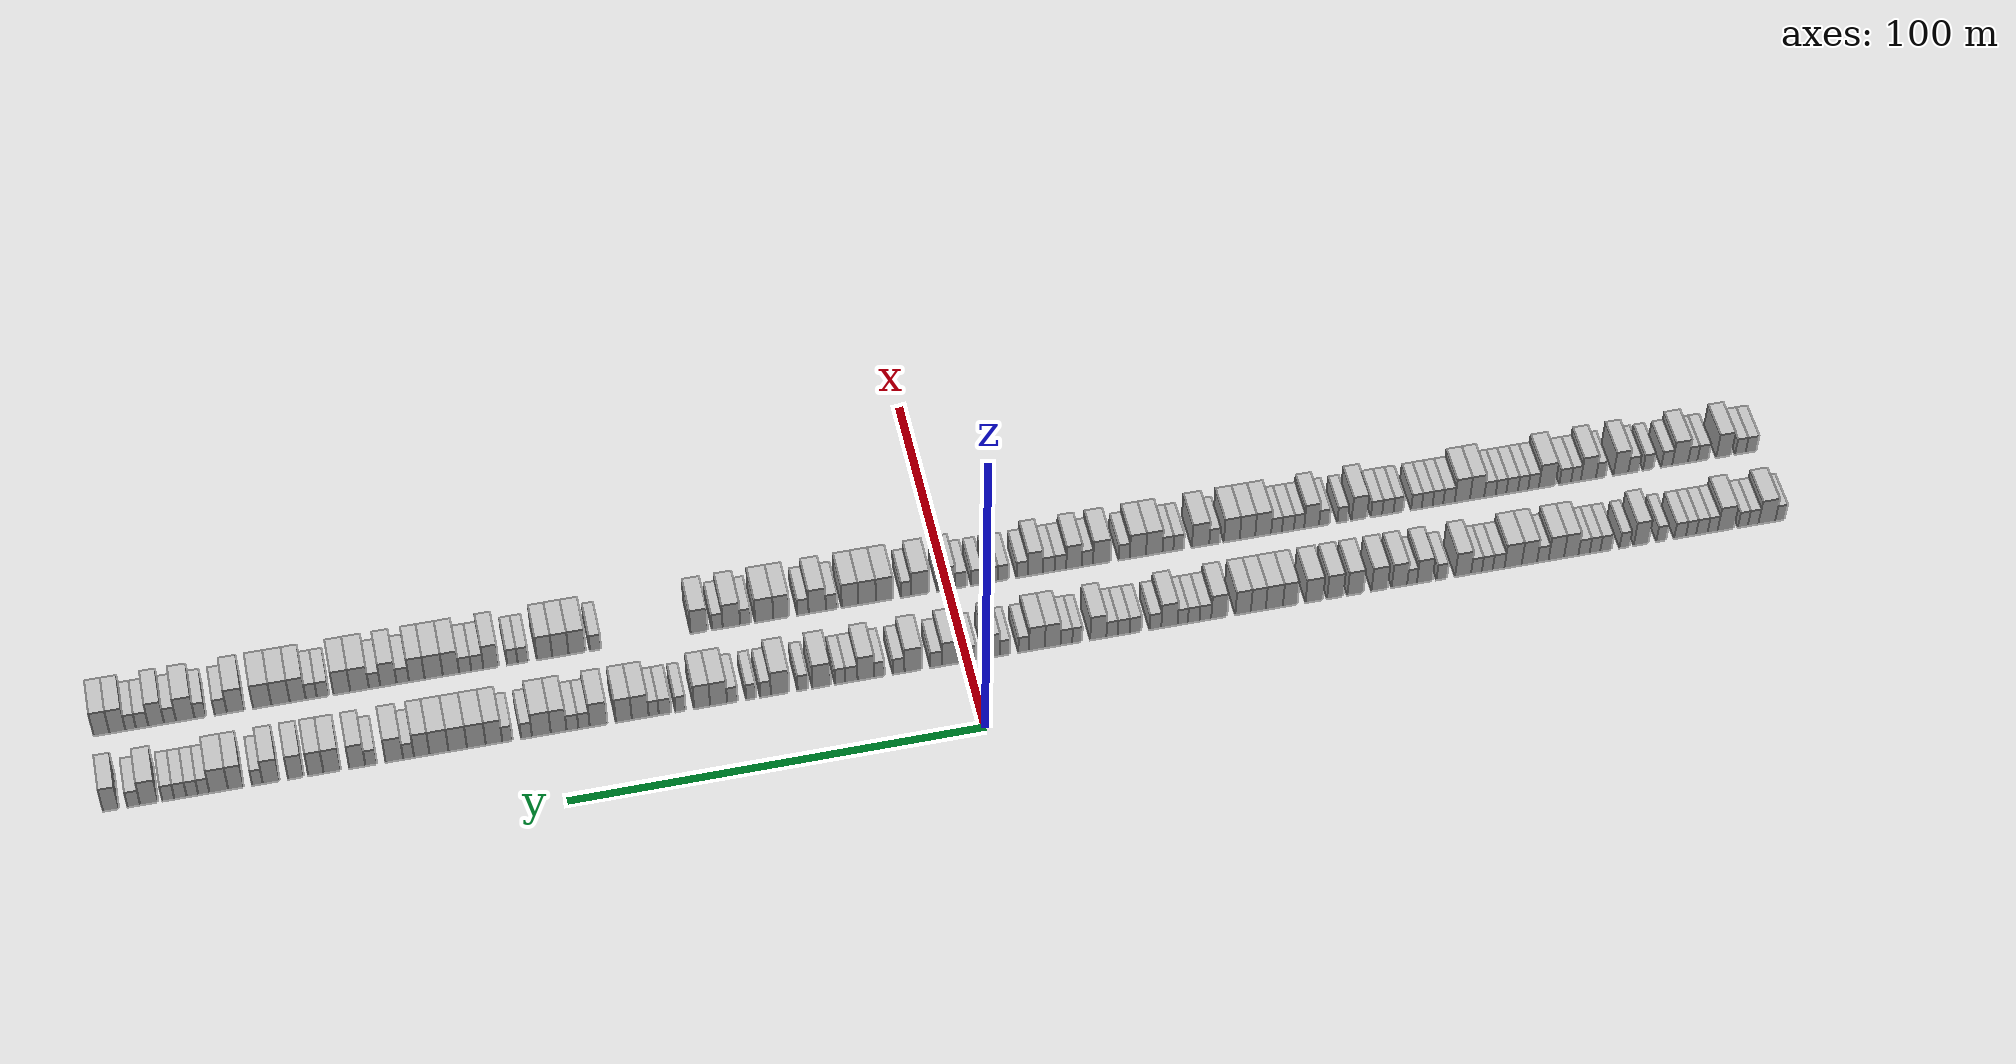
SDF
<sdf version="1.6">
 <world name="default">
  <scene>
   <sky><clouds><speed>12</speed></clouds></sky>
   <ambient>0.4 0.4 0.4 1</ambient>
   <background>0.7 0.7 0.7 1</background>
   <shadows>1</shadows>
  </scene>
  <gravity>0 0 -9.8066</gravity>
  <magnetic_field>6e-06 2.3e-05 -4.2e-05</magnetic_field>
  <physics default="0" name="default_physics" type="ode">
   <ode>
    <solver>
     <type>quick</type>
     <iters>10</iters>
     <sor>1.0</sor>
     <use_dynamic_moi_rescaling>0</use_dynamic_moi_rescaling>
    </solver>
    <constraints>
     <cfm>0</cfm>
     <erp>0.2</erp>
     <contact_max_correcting_vel>100</contact_max_correcting_vel>
     <contact_surface_layer>0.001</contact_surface_layer>
    </constraints>
   </ode>
   <max_step_size>0.004</max_step_size>
   <real_time_factor>1</real_time_factor>
   <real_time_update_rate>250</real_time_update_rate>
  </physics>
  <light name="sun" type="directional">
   <pose>0 0 10 0 0 0</pose>
   <diffuse>0.8 0.8 0.8 1</diffuse>
   <specular>0.2 0.2 0.2 1</specular>
   <attenuation>
    <range>1000</range>
    <constant>0.9</constant>
    <linear>0.01</linear>
    <quadratic>0.001</quadratic>
   </attenuation>
   <direction>-0.5 0.1 -0.9</direction>
  </light>
  <model name="building_1">
   <static>1</static>
   <pose>25.0000 -202.7834 0 0.000000 0.000000 0.000000</pose>
   <link name="link">
    <pose>0 0 3.00 0 0 0</pose>
    <collision name="collision"><geometry><box><size>10.0000 2.4333 6.0000</size></box></geometry></collision>
    <visual name="visual">
     <cast_shadows>0</cast_shadows>
     <geometry><box><size>10.0000 2.4333 6.0000</size></box></geometry>
     <material>
      <script>
       <uri>model://HANNAS_wall/materials/scripts</uri>
       <uri>model://HANNAS_wall/materials/textures</uri>
       <name>vrc/HANNAS_wall</name>
      </script>
     </material>
    </visual>
   </link>
  </model>
  <model name="building_2">
   <static>1</static>
   <pose>25.0000 -199.4211 0 0.000000 0.000000 0.000000</pose>
   <link name="link">
    <pose>0 0 4.50 0 0 0</pose>
    <collision name="collision"><geometry><box><size>10.0000 4.2912 9.0000</size></box></geometry></collision>
    <visual name="visual">
     <cast_shadows>0</cast_shadows>
     <geometry><box><size>10.0000 4.2912 9.0000</size></box></geometry>
     <material>
      <script>
       <uri>model://HANNAS_wall/materials/scripts</uri>
       <uri>model://HANNAS_wall/materials/textures</uri>
       <name>vrc/HANNAS_wall</name>
      </script>
     </material>
    </visual>
   </link>
  </model>
  <model name="building_3">
   <static>1</static>
   <pose>25.0000 -195.9313 0 0.000000 0.000000 0.000000</pose>
   <link name="link">
    <pose>0 0 3.00 0 0 0</pose>
    <collision name="collision"><geometry><box><size>10.0000 2.6886 6.0000</size></box></geometry></collision>
    <visual name="visual">
     <cast_shadows>0</cast_shadows>
     <geometry><box><size>10.0000 2.6886 6.0000</size></box></geometry>
     <material>
      <script>
       <uri>model://HANNAS_wall/materials/scripts</uri>
       <uri>model://HANNAS_wall/materials/textures</uri>
       <name>vrc/HANNAS_wall</name>
      </script>
     </material>
    </visual>
   </link>
  </model>
  <model name="building_4">
   <static>1</static>
   <pose>25.0000 -193.3184 0 0.000000 0.000000 0.000000</pose>
   <link name="link">
    <pose>0 0 3.00 0 0 0</pose>
    <collision name="collision"><geometry><box><size>10.0000 2.5372 6.0000</size></box></geometry></collision>
    <visual name="visual">
     <cast_shadows>0</cast_shadows>
     <geometry><box><size>10.0000 2.5372 6.0000</size></box></geometry>
     <material>
      <script>
       <uri>model://HANNAS_wall/materials/scripts</uri>
       <uri>model://HANNAS_wall/materials/textures</uri>
       <name>vrc/HANNAS_wall</name>
      </script>
     </material>
    </visual>
   </link>
  </model>
  <model name="building_5">
   <static>1</static>
   <pose>25.0000 -188.9515 0 0.000000 0.000000 0.000000</pose>
   <link name="link">
    <pose>0 0 4.50 0 0 0</pose>
    <collision name="collision"><geometry><box><size>10.0000 4.1965 9.0000</size></box></geometry></collision>
    <visual name="visual">
     <cast_shadows>0</cast_shadows>
     <geometry><box><size>10.0000 4.1965 9.0000</size></box></geometry>
     <material>
      <script>
       <uri>model://HANNAS_wall/materials/scripts</uri>
       <uri>model://HANNAS_wall/materials/textures</uri>
       <name>vrc/HANNAS_wall</name>
      </script>
     </material>
    </visual>
   </link>
  </model>
  <model name="building_6">
   <static>1</static>
   <pose>25.0000 -185.5904 0 0.000000 0.000000 0.000000</pose>
   <link name="link">
    <pose>0 0 3.00 0 0 0</pose>
    <collision name="collision"><geometry><box><size>10.0000 2.5256 6.0000</size></box></geometry></collision>
    <visual name="visual">
     <cast_shadows>0</cast_shadows>
     <geometry><box><size>10.0000 2.5256 6.0000</size></box></geometry>
     <material>
      <script>
       <uri>model://HANNAS_wall/materials/scripts</uri>
       <uri>model://HANNAS_wall/materials/textures</uri>
       <name>vrc/HANNAS_wall</name>
      </script>
     </material>
    </visual>
   </link>
  </model>
  <model name="building_7">
   <static>1</static>
   <pose>25.0000 -182.8566 0 0.000000 0.000000 0.000000</pose>
   <link name="link">
    <pose>0 0 3.00 0 0 0</pose>
    <collision name="collision"><geometry><box><size>10.0000 2.9419 6.0000</size></box></geometry></collision>
    <visual name="visual">
     <cast_shadows>0</cast_shadows>
     <geometry><box><size>10.0000 2.9419 6.0000</size></box></geometry>
     <material>
      <script>
       <uri>model://HANNAS_wall/materials/scripts</uri>
       <uri>model://HANNAS_wall/materials/textures</uri>
       <name>vrc/HANNAS_wall</name>
      </script>
     </material>
    </visual>
   </link>
  </model>
  <model name="building_8">
   <static>1</static>
   <pose>25.0000 -180.0870 0 0.000000 0.000000 0.000000</pose>
   <link name="link">
    <pose>0 0 3.00 0 0 0</pose>
    <collision name="collision"><geometry><box><size>10.0000 2.5973 6.0000</size></box></geometry></collision>
    <visual name="visual">
     <cast_shadows>0</cast_shadows>
     <geometry><box><size>10.0000 2.5973 6.0000</size></box></geometry>
     <material>
      <script>
       <uri>model://HANNAS_wall/materials/scripts</uri>
       <uri>model://HANNAS_wall/materials/textures</uri>
       <name>vrc/HANNAS_wall</name>
      </script>
     </material>
    </visual>
   </link>
  </model>
  <model name="building_9">
   <static>1</static>
   <pose>25.0000 -177.2991 0 0.000000 0.000000 0.000000</pose>
   <link name="link">
    <pose>0 0 3.00 0 0 0</pose>
    <collision name="collision"><geometry><box><size>10.0000 2.9786 6.0000</size></box></geometry></collision>
    <visual name="visual">
     <cast_shadows>0</cast_shadows>
     <geometry><box><size>10.0000 2.9786 6.0000</size></box></geometry>
     <material>
      <script>
       <uri>model://HANNAS_wall/materials/scripts</uri>
       <uri>model://HANNAS_wall/materials/textures</uri>
       <name>vrc/HANNAS_wall</name>
      </script>
     </material>
    </visual>
   </link>
  </model>
  <model name="building_10">
   <static>1</static>
   <pose>25.0000 -172.5464 0 0.000000 0.000000 0.000000</pose>
   <link name="link">
    <pose>0 0 3.00 0 0 0</pose>
    <collision name="collision"><geometry><box><size>10.0000 2.5269 6.0000</size></box></geometry></collision>
    <visual name="visual">
     <cast_shadows>0</cast_shadows>
     <geometry><box><size>10.0000 2.5269 6.0000</size></box></geometry>
     <material>
      <script>
       <uri>model://HANNAS_wall/materials/scripts</uri>
       <uri>model://HANNAS_wall/materials/textures</uri>
       <name>vrc/HANNAS_wall</name>
      </script>
     </material>
    </visual>
   </link>
  </model>
  <model name="building_11">
   <static>1</static>
   <pose>25.0000 -167.4018 0 0.000000 0.000000 0.000000</pose>
   <link name="link">
    <pose>0 0 4.50 0 0 0</pose>
    <collision name="collision"><geometry><box><size>10.0000 3.7622 9.0000</size></box></geometry></collision>
    <visual name="visual">
     <cast_shadows>0</cast_shadows>
     <geometry><box><size>10.0000 3.7622 9.0000</size></box></geometry>
     <material>
      <script>
       <uri>model://HANNAS_wall/materials/scripts</uri>
       <uri>model://HANNAS_wall/materials/textures</uri>
       <name>vrc/HANNAS_wall</name>
      </script>
     </material>
    </visual>
   </link>
  </model>
  <model name="building_12">
   <static>1</static>
   <pose>25.0000 -163.2231 0 0.000000 0.000000 0.000000</pose>
   <link name="link">
    <pose>0 0 3.00 0 0 0</pose>
    <collision name="collision"><geometry><box><size>10.0000 2.5953 6.0000</size></box></geometry></collision>
    <visual name="visual">
     <cast_shadows>0</cast_shadows>
     <geometry><box><size>10.0000 2.5953 6.0000</size></box></geometry>
     <material>
      <script>
       <uri>model://HANNAS_wall/materials/scripts</uri>
       <uri>model://HANNAS_wall/materials/textures</uri>
       <name>vrc/HANNAS_wall</name>
      </script>
     </material>
    </visual>
   </link>
  </model>
  <model name="building_13">
   <static>1</static>
   <pose>25.0000 -158.4871 0 0.000000 0.000000 0.000000</pose>
   <link name="link">
    <pose>0 0 3.00 0 0 0</pose>
    <collision name="collision"><geometry><box><size>10.0000 2.8767 6.0000</size></box></geometry></collision>
    <visual name="visual">
     <cast_shadows>0</cast_shadows>
     <geometry><box><size>10.0000 2.8767 6.0000</size></box></geometry>
     <material>
      <script>
       <uri>model://HANNAS_wall/materials/scripts</uri>
       <uri>model://HANNAS_wall/materials/textures</uri>
       <name>vrc/HANNAS_wall</name>
      </script>
     </material>
    </visual>
   </link>
  </model>
  <model name="building_14">
   <static>1</static>
   <pose>25.0000 -155.7029 0 0.000000 0.000000 0.000000</pose>
   <link name="link">
    <pose>0 0 3.00 0 0 0</pose>
    <collision name="collision"><geometry><box><size>10.0000 2.6917 6.0000</size></box></geometry></collision>
    <visual name="visual">
     <cast_shadows>0</cast_shadows>
     <geometry><box><size>10.0000 2.6917 6.0000</size></box></geometry>
     <material>
      <script>
       <uri>model://HANNAS_wall/materials/scripts</uri>
       <uri>model://HANNAS_wall/materials/textures</uri>
       <name>vrc/HANNAS_wall</name>
      </script>
     </material>
    </visual>
   </link>
  </model>
  <model name="building_15">
   <static>1</static>
   <pose>25.0000 -152.9369 0 0.000000 0.000000 0.000000</pose>
   <link name="link">
    <pose>0 0 3.00 0 0 0</pose>
    <collision name="collision"><geometry><box><size>10.0000 2.8404 6.0000</size></box></geometry></collision>
    <visual name="visual">
     <cast_shadows>0</cast_shadows>
     <geometry><box><size>10.0000 2.8404 6.0000</size></box></geometry>
     <material>
      <script>
       <uri>model://HANNAS_wall/materials/scripts</uri>
       <uri>model://HANNAS_wall/materials/textures</uri>
       <name>vrc/HANNAS_wall</name>
      </script>
     </material>
    </visual>
   </link>
  </model>
  <model name="building_16">
   <static>1</static>
   <pose>25.0000 -149.6994 0 0.000000 0.000000 0.000000</pose>
   <link name="link">
    <pose>0 0 4.50 0 0 0</pose>
    <collision name="collision"><geometry><box><size>10.0000 3.6344 9.0000</size></box></geometry></collision>
    <visual name="visual">
     <cast_shadows>0</cast_shadows>
     <geometry><box><size>10.0000 3.6344 9.0000</size></box></geometry>
     <material>
      <script>
       <uri>model://HANNAS_wall/materials/scripts</uri>
       <uri>model://HANNAS_wall/materials/textures</uri>
       <name>vrc/HANNAS_wall</name>
      </script>
     </material>
    </visual>
   </link>
  </model>
  <model name="building_17">
   <static>1</static>
   <pose>25.0000 -145.9331 0 0.000000 0.000000 0.000000</pose>
   <link name="link">
    <pose>0 0 4.50 0 0 0</pose>
    <collision name="collision"><geometry><box><size>10.0000 3.8982 9.0000</size></box></geometry></collision>
    <visual name="visual">
     <cast_shadows>0</cast_shadows>
     <geometry><box><size>10.0000 3.8982 9.0000</size></box></geometry>
     <material>
      <script>
       <uri>model://HANNAS_wall/materials/scripts</uri>
       <uri>model://HANNAS_wall/materials/textures</uri>
       <name>vrc/HANNAS_wall</name>
      </script>
     </material>
    </visual>
   </link>
  </model>
  <model name="building_18">
   <static>1</static>
   <pose>25.0000 -142.5305 0 0.000000 0.000000 0.000000</pose>
   <link name="link">
    <pose>0 0 3.00 0 0 0</pose>
    <collision name="collision"><geometry><box><size>10.0000 2.9070 6.0000</size></box></geometry></collision>
    <visual name="visual">
     <cast_shadows>0</cast_shadows>
     <geometry><box><size>10.0000 2.9070 6.0000</size></box></geometry>
     <material>
      <script>
       <uri>model://HANNAS_wall/materials/scripts</uri>
       <uri>model://HANNAS_wall/materials/textures</uri>
       <name>vrc/HANNAS_wall</name>
      </script>
     </material>
    </visual>
   </link>
  </model>
  <model name="building_19">
   <static>1</static>
   <pose>25.0000 -139.1296 0 0.000000 0.000000 0.000000</pose>
   <link name="link">
    <pose>0 0 4.50 0 0 0</pose>
    <collision name="collision"><geometry><box><size>10.0000 3.8948 9.0000</size></box></geometry></collision>
    <visual name="visual">
     <cast_shadows>0</cast_shadows>
     <geometry><box><size>10.0000 3.8948 9.0000</size></box></geometry>
     <material>
      <script>
       <uri>model://HANNAS_wall/materials/scripts</uri>
       <uri>model://HANNAS_wall/materials/textures</uri>
       <name>vrc/HANNAS_wall</name>
      </script>
     </material>
    </visual>
   </link>
  </model>
  <model name="building_20">
   <static>1</static>
   <pose>25.0000 -135.0204 0 0.000000 0.000000 0.000000</pose>
   <link name="link">
    <pose>0 0 4.50 0 0 0</pose>
    <collision name="collision"><geometry><box><size>10.0000 4.3237 9.0000</size></box></geometry></collision>
    <visual name="visual">
     <cast_shadows>0</cast_shadows>
     <geometry><box><size>10.0000 4.3237 9.0000</size></box></geometry>
     <material>
      <script>
       <uri>model://HANNAS_wall/materials/scripts</uri>
       <uri>model://HANNAS_wall/materials/textures</uri>
       <name>vrc/HANNAS_wall</name>
      </script>
     </material>
    </visual>
   </link>
  </model>
  <model name="building_21">
   <static>1</static>
   <pose>25.0000 -131.3810 0 0.000000 0.000000 0.000000</pose>
   <link name="link">
    <pose>0 0 3.00 0 0 0</pose>
    <collision name="collision"><geometry><box><size>10.0000 2.9551 6.0000</size></box></geometry></collision>
    <visual name="visual">
     <cast_shadows>0</cast_shadows>
     <geometry><box><size>10.0000 2.9551 6.0000</size></box></geometry>
     <material>
      <script>
       <uri>model://HANNAS_wall/materials/scripts</uri>
       <uri>model://HANNAS_wall/materials/textures</uri>
       <name>vrc/HANNAS_wall</name>
      </script>
     </material>
    </visual>
   </link>
  </model>
  <model name="building_22">
   <static>1</static>
   <pose>25.0000 -128.5316 0 0.000000 0.000000 0.000000</pose>
   <link name="link">
    <pose>0 0 3.00 0 0 0</pose>
    <collision name="collision"><geometry><box><size>10.0000 2.7437 6.0000</size></box></geometry></collision>
    <visual name="visual">
     <cast_shadows>0</cast_shadows>
     <geometry><box><size>10.0000 2.7437 6.0000</size></box></geometry>
     <material>
      <script>
       <uri>model://HANNAS_wall/materials/scripts</uri>
       <uri>model://HANNAS_wall/materials/textures</uri>
       <name>vrc/HANNAS_wall</name>
      </script>
     </material>
    </visual>
   </link>
  </model>
  <model name="building_23">
   <static>1</static>
   <pose>25.0000 -125.8042 0 0.000000 0.000000 0.000000</pose>
   <link name="link">
    <pose>0 0 3.00 0 0 0</pose>
    <collision name="collision"><geometry><box><size>10.0000 2.7111 6.0000</size></box></geometry></collision>
    <visual name="visual">
     <cast_shadows>0</cast_shadows>
     <geometry><box><size>10.0000 2.7111 6.0000</size></box></geometry>
     <material>
      <script>
       <uri>model://HANNAS_wall/materials/scripts</uri>
       <uri>model://HANNAS_wall/materials/textures</uri>
       <name>vrc/HANNAS_wall</name>
      </script>
     </material>
    </visual>
   </link>
  </model>
  <model name="building_24">
   <static>1</static>
   <pose>25.0000 -122.4449 0 0.000000 0.000000 0.000000</pose>
   <link name="link">
    <pose>0 0 4.50 0 0 0</pose>
    <collision name="collision"><geometry><box><size>10.0000 4.0074 9.0000</size></box></geometry></collision>
    <visual name="visual">
     <cast_shadows>0</cast_shadows>
     <geometry><box><size>10.0000 4.0074 9.0000</size></box></geometry>
     <material>
      <script>
       <uri>model://HANNAS_wall/materials/scripts</uri>
       <uri>model://HANNAS_wall/materials/textures</uri>
       <name>vrc/HANNAS_wall</name>
      </script>
     </material>
    </visual>
   </link>
  </model>
  <model name="building_25">
   <static>1</static>
   <pose>25.0000 -117.1076 0 0.000000 0.000000 0.000000</pose>
   <link name="link">
    <pose>0 0 3.00 0 0 0</pose>
    <collision name="collision"><geometry><box><size>10.0000 2.6671 6.0000</size></box></geometry></collision>
    <visual name="visual">
     <cast_shadows>0</cast_shadows>
     <geometry><box><size>10.0000 2.6671 6.0000</size></box></geometry>
     <material>
      <script>
       <uri>model://HANNAS_wall/materials/scripts</uri>
       <uri>model://HANNAS_wall/materials/textures</uri>
       <name>vrc/HANNAS_wall</name>
      </script>
     </material>
    </visual>
   </link>
  </model>
  <model name="building_26">
   <static>1</static>
   <pose>25.0000 -112.8133 0 0.000000 0.000000 0.000000</pose>
   <link name="link">
    <pose>0 0 4.50 0 0 0</pose>
    <collision name="collision"><geometry><box><size>10.0000 3.9217 9.0000</size></box></geometry></collision>
    <visual name="visual">
     <cast_shadows>0</cast_shadows>
     <geometry><box><size>10.0000 3.9217 9.0000</size></box></geometry>
     <material>
      <script>
       <uri>model://HANNAS_wall/materials/scripts</uri>
       <uri>model://HANNAS_wall/materials/textures</uri>
       <name>vrc/HANNAS_wall</name>
      </script>
     </material>
    </visual>
   </link>
  </model>
  <model name="building_27">
   <static>1</static>
   <pose>25.0000 -109.6304 0 0.000000 0.000000 0.000000</pose>
   <link name="link">
    <pose>0 0 3.00 0 0 0</pose>
    <collision name="collision"><geometry><box><size>10.0000 2.4440 6.0000</size></box></geometry></collision>
    <visual name="visual">
     <cast_shadows>0</cast_shadows>
     <geometry><box><size>10.0000 2.4440 6.0000</size></box></geometry>
     <material>
      <script>
       <uri>model://HANNAS_wall/materials/scripts</uri>
       <uri>model://HANNAS_wall/materials/textures</uri>
       <name>vrc/HANNAS_wall</name>
      </script>
     </material>
    </visual>
   </link>
  </model>
  <model name="building_28">
   <static>1</static>
   <pose>25.0000 -106.4745 0 0.000000 0.000000 0.000000</pose>
   <link name="link">
    <pose>0 0 4.50 0 0 0</pose>
    <collision name="collision"><geometry><box><size>10.0000 3.8679 9.0000</size></box></geometry></collision>
    <visual name="visual">
     <cast_shadows>0</cast_shadows>
     <geometry><box><size>10.0000 3.8679 9.0000</size></box></geometry>
     <material>
      <script>
       <uri>model://HANNAS_wall/materials/scripts</uri>
       <uri>model://HANNAS_wall/materials/textures</uri>
       <name>vrc/HANNAS_wall</name>
      </script>
     </material>
    </visual>
   </link>
  </model>
  <model name="building_29">
   <static>1</static>
   <pose>25.0000 -101.5200 0 0.000000 0.000000 0.000000</pose>
   <link name="link">
    <pose>0 0 4.50 0 0 0</pose>
    <collision name="collision"><geometry><box><size>10.0000 4.0411 9.0000</size></box></geometry></collision>
    <visual name="visual">
     <cast_shadows>0</cast_shadows>
     <geometry><box><size>10.0000 4.0411 9.0000</size></box></geometry>
     <material>
      <script>
       <uri>model://HANNAS_wall/materials/scripts</uri>
       <uri>model://HANNAS_wall/materials/textures</uri>
       <name>vrc/HANNAS_wall</name>
      </script>
     </material>
    </visual>
   </link>
  </model>
  <model name="building_30">
   <static>1</static>
   <pose>25.0000 -95.4917 0 0.000000 0.000000 0.000000</pose>
   <link name="link">
    <pose>0 0 4.50 0 0 0</pose>
    <collision name="collision"><geometry><box><size>10.0000 4.0156 9.0000</size></box></geometry></collision>
    <visual name="visual">
     <cast_shadows>0</cast_shadows>
     <geometry><box><size>10.0000 4.0156 9.0000</size></box></geometry>
     <material>
      <script>
       <uri>model://HANNAS_wall/materials/scripts</uri>
       <uri>model://HANNAS_wall/materials/textures</uri>
       <name>vrc/HANNAS_wall</name>
      </script>
     </material>
    </visual>
   </link>
  </model>
  <model name="building_31">
   <static>1</static>
   <pose>25.0000 -90.4538 0 0.000000 0.000000 0.000000</pose>
   <link name="link">
    <pose>0 0 4.50 0 0 0</pose>
    <collision name="collision"><geometry><box><size>10.0000 4.0603 9.0000</size></box></geometry></collision>
    <visual name="visual">
     <cast_shadows>0</cast_shadows>
     <geometry><box><size>10.0000 4.0603 9.0000</size></box></geometry>
     <material>
      <script>
       <uri>model://HANNAS_wall/materials/scripts</uri>
       <uri>model://HANNAS_wall/materials/textures</uri>
       <name>vrc/HANNAS_wall</name>
      </script>
     </material>
    </visual>
   </link>
  </model>
  <model name="building_32">
   <static>1</static>
   <pose>25.0000 -85.2366 0 0.000000 0.000000 0.000000</pose>
   <link name="link">
    <pose>0 0 4.50 0 0 0</pose>
    <collision name="collision"><geometry><box><size>10.0000 4.3740 9.0000</size></box></geometry></collision>
    <visual name="visual">
     <cast_shadows>0</cast_shadows>
     <geometry><box><size>10.0000 4.3740 9.0000</size></box></geometry>
     <material>
      <script>
       <uri>model://HANNAS_wall/materials/scripts</uri>
       <uri>model://HANNAS_wall/materials/textures</uri>
       <name>vrc/HANNAS_wall</name>
      </script>
     </material>
    </visual>
   </link>
  </model>
  <model name="building_33">
   <static>1</static>
   <pose>25.0000 -79.2370 0 0.000000 0.000000 0.000000</pose>
   <link name="link">
    <pose>0 0 4.50 0 0 0</pose>
    <collision name="collision"><geometry><box><size>10.0000 3.6253 9.0000</size></box></geometry></collision>
    <visual name="visual">
     <cast_shadows>0</cast_shadows>
     <geometry><box><size>10.0000 3.6253 9.0000</size></box></geometry>
     <material>
      <script>
       <uri>model://HANNAS_wall/materials/scripts</uri>
       <uri>model://HANNAS_wall/materials/textures</uri>
       <name>vrc/HANNAS_wall</name>
      </script>
     </material>
    </visual>
   </link>
  </model>
  <model name="building_34">
   <static>1</static>
   <pose>25.0000 -75.3011 0 0.000000 0.000000 0.000000</pose>
   <link name="link">
    <pose>0 0 4.50 0 0 0</pose>
    <collision name="collision"><geometry><box><size>10.0000 4.2464 9.0000</size></box></geometry></collision>
    <visual name="visual">
     <cast_shadows>0</cast_shadows>
     <geometry><box><size>10.0000 4.2464 9.0000</size></box></geometry>
     <material>
      <script>
       <uri>model://HANNAS_wall/materials/scripts</uri>
       <uri>model://HANNAS_wall/materials/textures</uri>
       <name>vrc/HANNAS_wall</name>
      </script>
     </material>
    </visual>
   </link>
  </model>
  <model name="building_35">
   <static>1</static>
   <pose>25.0000 -71.3267 0 0.000000 0.000000 0.000000</pose>
   <link name="link">
    <pose>0 0 4.50 0 0 0</pose>
    <collision name="collision"><geometry><box><size>10.0000 3.7024 9.0000</size></box></geometry></collision>
    <visual name="visual">
     <cast_shadows>0</cast_shadows>
     <geometry><box><size>10.0000 3.7024 9.0000</size></box></geometry>
     <material>
      <script>
       <uri>model://HANNAS_wall/materials/scripts</uri>
       <uri>model://HANNAS_wall/materials/textures</uri>
       <name>vrc/HANNAS_wall</name>
      </script>
     </material>
    </visual>
   </link>
  </model>
  <model name="building_36">
   <static>1</static>
   <pose>25.0000 -67.5447 0 0.000000 0.000000 0.000000</pose>
   <link name="link">
    <pose>0 0 4.50 0 0 0</pose>
    <collision name="collision"><geometry><box><size>10.0000 3.8614 9.0000</size></box></geometry></collision>
    <visual name="visual">
     <cast_shadows>0</cast_shadows>
     <geometry><box><size>10.0000 3.8614 9.0000</size></box></geometry>
     <material>
      <script>
       <uri>model://HANNAS_wall/materials/scripts</uri>
       <uri>model://HANNAS_wall/materials/textures</uri>
       <name>vrc/HANNAS_wall</name>
      </script>
     </material>
    </visual>
   </link>
  </model>
  <model name="building_37">
   <static>1</static>
   <pose>25.0000 -61.6265 0 0.000000 0.000000 0.000000</pose>
   <link name="link">
    <pose>0 0 4.50 0 0 0</pose>
    <collision name="collision"><geometry><box><size>10.0000 3.9751 9.0000</size></box></geometry></collision>
    <visual name="visual">
     <cast_shadows>0</cast_shadows>
     <geometry><box><size>10.0000 3.9751 9.0000</size></box></geometry>
     <material>
      <script>
       <uri>model://HANNAS_wall/materials/scripts</uri>
       <uri>model://HANNAS_wall/materials/textures</uri>
       <name>vrc/HANNAS_wall</name>
      </script>
     </material>
    </visual>
   </link>
  </model>
  <model name="building_38">
   <static>1</static>
   <pose>25.0000 -58.1998 0 0.000000 0.000000 0.000000</pose>
   <link name="link">
    <pose>0 0 3.00 0 0 0</pose>
    <collision name="collision"><geometry><box><size>10.0000 2.8782 6.0000</size></box></geometry></collision>
    <visual name="visual">
     <cast_shadows>0</cast_shadows>
     <geometry><box><size>10.0000 2.8782 6.0000</size></box></geometry>
     <material>
      <script>
       <uri>model://HANNAS_wall/materials/scripts</uri>
       <uri>model://HANNAS_wall/materials/textures</uri>
       <name>vrc/HANNAS_wall</name>
      </script>
     </material>
    </visual>
   </link>
  </model>
  <model name="building_39">
   <static>1</static>
   <pose>25.0000 -55.3088 0 0.000000 0.000000 0.000000</pose>
   <link name="link">
    <pose>0 0 3.00 0 0 0</pose>
    <collision name="collision"><geometry><box><size>10.0000 2.9037 6.0000</size></box></geometry></collision>
    <visual name="visual">
     <cast_shadows>0</cast_shadows>
     <geometry><box><size>10.0000 2.9037 6.0000</size></box></geometry>
     <material>
      <script>
       <uri>model://HANNAS_wall/materials/scripts</uri>
       <uri>model://HANNAS_wall/materials/textures</uri>
       <name>vrc/HANNAS_wall</name>
      </script>
     </material>
    </visual>
   </link>
  </model>
  <model name="building_40">
   <static>1</static>
   <pose>25.0000 -52.5895 0 0.000000 0.000000 0.000000</pose>
   <link name="link">
    <pose>0 0 3.00 0 0 0</pose>
    <collision name="collision"><geometry><box><size>10.0000 2.5350 6.0000</size></box></geometry></collision>
    <visual name="visual">
     <cast_shadows>0</cast_shadows>
     <geometry><box><size>10.0000 2.5350 6.0000</size></box></geometry>
     <material>
      <script>
       <uri>model://HANNAS_wall/materials/scripts</uri>
       <uri>model://HANNAS_wall/materials/textures</uri>
       <name>vrc/HANNAS_wall</name>
      </script>
     </material>
    </visual>
   </link>
  </model>
  <model name="building_41">
   <static>1</static>
   <pose>25.0000 -49.3044 0 0.000000 0.000000 0.000000</pose>
   <link name="link">
    <pose>0 0 4.50 0 0 0</pose>
    <collision name="collision"><geometry><box><size>10.0000 4.0352 9.0000</size></box></geometry></collision>
    <visual name="visual">
     <cast_shadows>0</cast_shadows>
     <geometry><box><size>10.0000 4.0352 9.0000</size></box></geometry>
     <material>
      <script>
       <uri>model://HANNAS_wall/materials/scripts</uri>
       <uri>model://HANNAS_wall/materials/textures</uri>
       <name>vrc/HANNAS_wall</name>
      </script>
     </material>
    </visual>
   </link>
  </model>
  <model name="building_42">
   <static>1</static>
   <pose>25.0000 -45.8358 0 0.000000 0.000000 0.000000</pose>
   <link name="link">
    <pose>0 0 3.00 0 0 0</pose>
    <collision name="collision"><geometry><box><size>10.0000 2.9020 6.0000</size></box></geometry></collision>
    <visual name="visual">
     <cast_shadows>0</cast_shadows>
     <geometry><box><size>10.0000 2.9020 6.0000</size></box></geometry>
     <material>
      <script>
       <uri>model://HANNAS_wall/materials/scripts</uri>
       <uri>model://HANNAS_wall/materials/textures</uri>
       <name>vrc/HANNAS_wall</name>
      </script>
     </material>
    </visual>
   </link>
  </model>
  <model name="building_43">
   <static>1</static>
   <pose>25.0000 -40.9486 0 0.000000 0.000000 0.000000</pose>
   <link name="link">
    <pose>0 0 3.00 0 0 0</pose>
    <collision name="collision"><geometry><box><size>10.0000 2.8724 6.0000</size></box></geometry></collision>
    <visual name="visual">
     <cast_shadows>0</cast_shadows>
     <geometry><box><size>10.0000 2.8724 6.0000</size></box></geometry>
     <material>
      <script>
       <uri>model://HANNAS_wall/materials/scripts</uri>
       <uri>model://HANNAS_wall/materials/textures</uri>
       <name>vrc/HANNAS_wall</name>
      </script>
     </material>
    </visual>
   </link>
  </model>
  <model name="building_44">
   <static>1</static>
   <pose>25.0000 -38.0196 0 0.000000 0.000000 0.000000</pose>
   <link name="link">
    <pose>0 0 3.00 0 0 0</pose>
    <collision name="collision"><geometry><box><size>10.0000 2.9856 6.0000</size></box></geometry></collision>
    <visual name="visual">
     <cast_shadows>0</cast_shadows>
     <geometry><box><size>10.0000 2.9856 6.0000</size></box></geometry>
     <material>
      <script>
       <uri>model://HANNAS_wall/materials/scripts</uri>
       <uri>model://HANNAS_wall/materials/textures</uri>
       <name>vrc/HANNAS_wall</name>
      </script>
     </material>
    </visual>
   </link>
  </model>
  <model name="building_45">
   <static>1</static>
   <pose>25.0000 -35.1479 0 0.000000 0.000000 0.000000</pose>
   <link name="link">
    <pose>0 0 3.00 0 0 0</pose>
    <collision name="collision"><geometry><box><size>10.0000 2.7579 6.0000</size></box></geometry></collision>
    <visual name="visual">
     <cast_shadows>0</cast_shadows>
     <geometry><box><size>10.0000 2.7579 6.0000</size></box></geometry>
     <material>
      <script>
       <uri>model://HANNAS_wall/materials/scripts</uri>
       <uri>model://HANNAS_wall/materials/textures</uri>
       <name>vrc/HANNAS_wall</name>
      </script>
     </material>
    </visual>
   </link>
  </model>
  <model name="building_46">
   <static>1</static>
   <pose>25.0000 -31.7812 0 0.000000 0.000000 0.000000</pose>
   <link name="link">
    <pose>0 0 4.50 0 0 0</pose>
    <collision name="collision"><geometry><box><size>10.0000 3.9755 9.0000</size></box></geometry></collision>
    <visual name="visual">
     <cast_shadows>0</cast_shadows>
     <geometry><box><size>10.0000 3.9755 9.0000</size></box></geometry>
     <material>
      <script>
       <uri>model://HANNAS_wall/materials/scripts</uri>
       <uri>model://HANNAS_wall/materials/textures</uri>
       <name>vrc/HANNAS_wall</name>
      </script>
     </material>
    </visual>
   </link>
  </model>
  <model name="building_47">
   <static>1</static>
   <pose>25.0000 -26.5902 0 0.000000 0.000000 0.000000</pose>
   <link name="link">
    <pose>0 0 3.00 0 0 0</pose>
    <collision name="collision"><geometry><box><size>10.0000 2.4067 6.0000</size></box></geometry></collision>
    <visual name="visual">
     <cast_shadows>0</cast_shadows>
     <geometry><box><size>10.0000 2.4067 6.0000</size></box></geometry>
     <material>
      <script>
       <uri>model://HANNAS_wall/materials/scripts</uri>
       <uri>model://HANNAS_wall/materials/textures</uri>
       <name>vrc/HANNAS_wall</name>
      </script>
     </material>
    </visual>
   </link>
  </model>
  <model name="building_48">
   <static>1</static>
   <pose>25.0000 -23.9397 0 0.000000 0.000000 0.000000</pose>
   <link name="link">
    <pose>0 0 3.00 0 0 0</pose>
    <collision name="collision"><geometry><box><size>10.0000 2.8944 6.0000</size></box></geometry></collision>
    <visual name="visual">
     <cast_shadows>0</cast_shadows>
     <geometry><box><size>10.0000 2.8944 6.0000</size></box></geometry>
     <material>
      <script>
       <uri>model://HANNAS_wall/materials/scripts</uri>
       <uri>model://HANNAS_wall/materials/textures</uri>
       <name>vrc/HANNAS_wall</name>
      </script>
     </material>
    </visual>
   </link>
  </model>
  <model name="building_49">
   <static>1</static>
   <pose>25.0000 -20.5937 0 0.000000 0.000000 0.000000</pose>
   <link name="link">
    <pose>0 0 4.50 0 0 0</pose>
    <collision name="collision"><geometry><box><size>10.0000 3.7975 9.0000</size></box></geometry></collision>
    <visual name="visual">
     <cast_shadows>0</cast_shadows>
     <geometry><box><size>10.0000 3.7975 9.0000</size></box></geometry>
     <material>
      <script>
       <uri>model://HANNAS_wall/materials/scripts</uri>
       <uri>model://HANNAS_wall/materials/textures</uri>
       <name>vrc/HANNAS_wall</name>
      </script>
     </material>
    </visual>
   </link>
  </model>
  <model name="building_50">
   <static>1</static>
   <pose>25.0000 -16.7432 0 0.000000 0.000000 0.000000</pose>
   <link name="link">
    <pose>0 0 4.50 0 0 0</pose>
    <collision name="collision"><geometry><box><size>10.0000 3.9035 9.0000</size></box></geometry></collision>
    <visual name="visual">
     <cast_shadows>0</cast_shadows>
     <geometry><box><size>10.0000 3.9035 9.0000</size></box></geometry>
     <material>
      <script>
       <uri>model://HANNAS_wall/materials/scripts</uri>
       <uri>model://HANNAS_wall/materials/textures</uri>
       <name>vrc/HANNAS_wall</name>
      </script>
     </material>
    </visual>
   </link>
  </model>
  <model name="building_51">
   <static>1</static>
   <pose>25.0000 -13.4759 0 0.000000 0.000000 0.000000</pose>
   <link name="link">
    <pose>0 0 3.00 0 0 0</pose>
    <collision name="collision"><geometry><box><size>10.0000 2.6311 6.0000</size></box></geometry></collision>
    <visual name="visual">
     <cast_shadows>0</cast_shadows>
     <geometry><box><size>10.0000 2.6311 6.0000</size></box></geometry>
     <material>
      <script>
       <uri>model://HANNAS_wall/materials/scripts</uri>
       <uri>model://HANNAS_wall/materials/textures</uri>
       <name>vrc/HANNAS_wall</name>
      </script>
     </material>
    </visual>
   </link>
  </model>
  <model name="building_52">
   <static>1</static>
   <pose>25.0000 -8.8970 0 0.000000 0.000000 0.000000</pose>
   <link name="link">
    <pose>0 0 3.00 0 0 0</pose>
    <collision name="collision"><geometry><box><size>10.0000 2.5266 6.0000</size></box></geometry></collision>
    <visual name="visual">
     <cast_shadows>0</cast_shadows>
     <geometry><box><size>10.0000 2.5266 6.0000</size></box></geometry>
     <material>
      <script>
       <uri>model://HANNAS_wall/materials/scripts</uri>
       <uri>model://HANNAS_wall/materials/textures</uri>
       <name>vrc/HANNAS_wall</name>
      </script>
     </material>
    </visual>
   </link>
  </model>
  <model name="building_53">
   <static>1</static>
   <pose>25.0000 -5.7315 0 0.000000 0.000000 0.000000</pose>
   <link name="link">
    <pose>0 0 4.50 0 0 0</pose>
    <collision name="collision"><geometry><box><size>10.0000 3.8044 9.0000</size></box></geometry></collision>
    <visual name="visual">
     <cast_shadows>0</cast_shadows>
     <geometry><box><size>10.0000 3.8044 9.0000</size></box></geometry>
     <material>
      <script>
       <uri>model://HANNAS_wall/materials/scripts</uri>
       <uri>model://HANNAS_wall/materials/textures</uri>
       <name>vrc/HANNAS_wall</name>
      </script>
     </material>
    </visual>
   </link>
  </model>
  <model name="building_54">
   <static>1</static>
   <pose>25.0000 -0.4231 0 0.000000 0.000000 0.000000</pose>
   <link name="link">
    <pose>0 0 3.00 0 0 0</pose>
    <collision name="collision"><geometry><box><size>10.0000 2.8125 6.0000</size></box></geometry></collision>
    <visual name="visual">
     <cast_shadows>0</cast_shadows>
     <geometry><box><size>10.0000 2.8125 6.0000</size></box></geometry>
     <material>
      <script>
       <uri>model://HANNAS_wall/materials/scripts</uri>
       <uri>model://HANNAS_wall/materials/textures</uri>
       <name>vrc/HANNAS_wall</name>
      </script>
     </material>
    </visual>
   </link>
  </model>
  <model name="building_55">
   <static>1</static>
   <pose>25.0000 4.2093 0 0.000000 0.000000 0.000000</pose>
   <link name="link">
    <pose>0 0 4.50 0 0 0</pose>
    <collision name="collision"><geometry><box><size>10.0000 4.4522 9.0000</size></box></geometry></collision>
    <visual name="visual">
     <cast_shadows>0</cast_shadows>
     <geometry><box><size>10.0000 4.4522 9.0000</size></box></geometry>
     <material>
      <script>
       <uri>model://HANNAS_wall/materials/scripts</uri>
       <uri>model://HANNAS_wall/materials/textures</uri>
       <name>vrc/HANNAS_wall</name>
      </script>
     </material>
    </visual>
   </link>
  </model>
  <model name="building_56">
   <static>1</static>
   <pose>25.0000 7.8749 0 0.000000 0.000000 0.000000</pose>
   <link name="link">
    <pose>0 0 3.00 0 0 0</pose>
    <collision name="collision"><geometry><box><size>10.0000 2.8789 6.0000</size></box></geometry></collision>
    <visual name="visual">
     <cast_shadows>0</cast_shadows>
     <geometry><box><size>10.0000 2.8789 6.0000</size></box></geometry>
     <material>
      <script>
       <uri>model://HANNAS_wall/materials/scripts</uri>
       <uri>model://HANNAS_wall/materials/textures</uri>
       <name>vrc/HANNAS_wall</name>
      </script>
     </material>
    </visual>
   </link>
  </model>
  <model name="building_57">
   <static>1</static>
   <pose>25.0000 13.4722 0 0.000000 0.000000 0.000000</pose>
   <link name="link">
    <pose>0 0 4.50 0 0 0</pose>
    <collision name="collision"><geometry><box><size>10.0000 4.3157 9.0000</size></box></geometry></collision>
    <visual name="visual">
     <cast_shadows>0</cast_shadows>
     <geometry><box><size>10.0000 4.3157 9.0000</size></box></geometry>
     <material>
      <script>
       <uri>model://HANNAS_wall/materials/scripts</uri>
       <uri>model://HANNAS_wall/materials/textures</uri>
       <name>vrc/HANNAS_wall</name>
      </script>
     </material>
    </visual>
   </link>
  </model>
  <model name="building_58">
   <static>1</static>
   <pose>25.0000 17.0487 0 0.000000 0.000000 0.000000</pose>
   <link name="link">
    <pose>0 0 3.00 0 0 0</pose>
    <collision name="collision"><geometry><box><size>10.0000 2.8374 6.0000</size></box></geometry></collision>
    <visual name="visual">
     <cast_shadows>0</cast_shadows>
     <geometry><box><size>10.0000 2.8374 6.0000</size></box></geometry>
     <material>
      <script>
       <uri>model://HANNAS_wall/materials/scripts</uri>
       <uri>model://HANNAS_wall/materials/textures</uri>
       <name>vrc/HANNAS_wall</name>
      </script>
     </material>
    </visual>
   </link>
  </model>
  <model name="building_59">
   <static>1</static>
   <pose>25.0000 21.7170 0 0.000000 0.000000 0.000000</pose>
   <link name="link">
    <pose>0 0 3.00 0 0 0</pose>
    <collision name="collision"><geometry><box><size>10.0000 2.4991 6.0000</size></box></geometry></collision>
    <visual name="visual">
     <cast_shadows>0</cast_shadows>
     <geometry><box><size>10.0000 2.4991 6.0000</size></box></geometry>
     <material>
      <script>
       <uri>model://HANNAS_wall/materials/scripts</uri>
       <uri>model://HANNAS_wall/materials/textures</uri>
       <name>vrc/HANNAS_wall</name>
      </script>
     </material>
    </visual>
   </link>
  </model>
  <model name="building_60">
   <static>1</static>
   <pose>25.0000 25.0026 0 0.000000 0.000000 0.000000</pose>
   <link name="link">
    <pose>0 0 4.50 0 0 0</pose>
    <collision name="collision"><geometry><box><size>10.0000 4.0722 9.0000</size></box></geometry></collision>
    <visual name="visual">
     <cast_shadows>0</cast_shadows>
     <geometry><box><size>10.0000 4.0722 9.0000</size></box></geometry>
     <material>
      <script>
       <uri>model://HANNAS_wall/materials/scripts</uri>
       <uri>model://HANNAS_wall/materials/textures</uri>
       <name>vrc/HANNAS_wall</name>
      </script>
     </material>
    </visual>
   </link>
  </model>
  <model name="building_61">
   <static>1</static>
   <pose>25.0000 28.5138 0 0.000000 0.000000 0.000000</pose>
   <link name="link">
    <pose>0 0 3.00 0 0 0</pose>
    <collision name="collision"><geometry><box><size>10.0000 2.9501 6.0000</size></box></geometry></collision>
    <visual name="visual">
     <cast_shadows>0</cast_shadows>
     <geometry><box><size>10.0000 2.9501 6.0000</size></box></geometry>
     <material>
      <script>
       <uri>model://HANNAS_wall/materials/scripts</uri>
       <uri>model://HANNAS_wall/materials/textures</uri>
       <name>vrc/HANNAS_wall</name>
      </script>
     </material>
    </visual>
   </link>
  </model>
  <model name="building_62">
   <static>1</static>
   <pose>25.0000 31.2584 0 0.000000 0.000000 0.000000</pose>
   <link name="link">
    <pose>0 0 3.00 0 0 0</pose>
    <collision name="collision"><geometry><box><size>10.0000 2.5391 6.0000</size></box></geometry></collision>
    <visual name="visual">
     <cast_shadows>0</cast_shadows>
     <geometry><box><size>10.0000 2.5391 6.0000</size></box></geometry>
     <material>
      <script>
       <uri>model://HANNAS_wall/materials/scripts</uri>
       <uri>model://HANNAS_wall/materials/textures</uri>
       <name>vrc/HANNAS_wall</name>
      </script>
     </material>
    </visual>
   </link>
  </model>
  <model name="building_63">
   <static>1</static>
   <pose>25.0000 35.7606 0 0.000000 0.000000 0.000000</pose>
   <link name="link">
    <pose>0 0 4.50 0 0 0</pose>
    <collision name="collision"><geometry><box><size>10.0000 4.4652 9.0000</size></box></geometry></collision>
    <visual name="visual">
     <cast_shadows>0</cast_shadows>
     <geometry><box><size>10.0000 4.4652 9.0000</size></box></geometry>
     <material>
      <script>
       <uri>model://HANNAS_wall/materials/scripts</uri>
       <uri>model://HANNAS_wall/materials/textures</uri>
       <name>vrc/HANNAS_wall</name>
      </script>
     </material>
    </visual>
   </link>
  </model>
  <model name="building_64">
   <static>1</static>
   <pose>25.0000 40.2761 0 0.000000 0.000000 0.000000</pose>
   <link name="link">
    <pose>0 0 3.00 0 0 0</pose>
    <collision name="collision"><geometry><box><size>10.0000 2.5658 6.0000</size></box></geometry></collision>
    <visual name="visual">
     <cast_shadows>0</cast_shadows>
     <geometry><box><size>10.0000 2.5658 6.0000</size></box></geometry>
     <material>
      <script>
       <uri>model://HANNAS_wall/materials/scripts</uri>
       <uri>model://HANNAS_wall/materials/textures</uri>
       <name>vrc/HANNAS_wall</name>
      </script>
     </material>
    </visual>
   </link>
  </model>
  <model name="building_65">
   <static>1</static>
   <pose>25.0000 45.7826 0 0.000000 0.000000 0.000000</pose>
   <link name="link">
    <pose>0 0 4.50 0 0 0</pose>
    <collision name="collision"><geometry><box><size>10.0000 4.4473 9.0000</size></box></geometry></collision>
    <visual name="visual">
     <cast_shadows>0</cast_shadows>
     <geometry><box><size>10.0000 4.4473 9.0000</size></box></geometry>
     <material>
      <script>
       <uri>model://HANNAS_wall/materials/scripts</uri>
       <uri>model://HANNAS_wall/materials/textures</uri>
       <name>vrc/HANNAS_wall</name>
      </script>
     </material>
    </visual>
   </link>
  </model>
  <model name="building_66">
   <static>1</static>
   <pose>25.0000 49.3003 0 0.000000 0.000000 0.000000</pose>
   <link name="link">
    <pose>0 0 3.00 0 0 0</pose>
    <collision name="collision"><geometry><box><size>10.0000 2.5882 6.0000</size></box></geometry></collision>
    <visual name="visual">
     <cast_shadows>0</cast_shadows>
     <geometry><box><size>10.0000 2.5882 6.0000</size></box></geometry>
     <material>
      <script>
       <uri>model://HANNAS_wall/materials/scripts</uri>
       <uri>model://HANNAS_wall/materials/textures</uri>
       <name>vrc/HANNAS_wall</name>
      </script>
     </material>
    </visual>
   </link>
  </model>
  <model name="building_67">
   <static>1</static>
   <pose>25.0000 52.7981 0 0.000000 0.000000 0.000000</pose>
   <link name="link">
    <pose>0 0 3.00 0 0 0</pose>
    <collision name="collision"><geometry><box><size>10.0000 2.4072 6.0000</size></box></geometry></collision>
    <visual name="visual">
     <cast_shadows>0</cast_shadows>
     <geometry><box><size>10.0000 2.4072 6.0000</size></box></geometry>
     <material>
      <script>
       <uri>model://HANNAS_wall/materials/scripts</uri>
       <uri>model://HANNAS_wall/materials/textures</uri>
       <name>vrc/HANNAS_wall</name>
      </script>
     </material>
    </visual>
   </link>
  </model>
  <model name="building_68">
   <static>1</static>
   <pose>25.0000 57.2887 0 0.000000 0.000000 0.000000</pose>
   <link name="link">
    <pose>0 0 3.00 0 0 0</pose>
    <collision name="collision"><geometry><box><size>10.0000 2.5740 6.0000</size></box></geometry></collision>
    <visual name="visual">
     <cast_shadows>0</cast_shadows>
     <geometry><box><size>10.0000 2.5740 6.0000</size></box></geometry>
     <material>
      <script>
       <uri>model://HANNAS_wall/materials/scripts</uri>
       <uri>model://HANNAS_wall/materials/textures</uri>
       <name>vrc/HANNAS_wall</name>
      </script>
     </material>
    </visual>
   </link>
  </model>
  <model name="building_69">
   <static>1</static>
   <pose>25.0000 60.6281 0 0.000000 0.000000 0.000000</pose>
   <link name="link">
    <pose>0 0 4.50 0 0 0</pose>
    <collision name="collision"><geometry><box><size>10.0000 4.1049 9.0000</size></box></geometry></collision>
    <visual name="visual">
     <cast_shadows>0</cast_shadows>
     <geometry><box><size>10.0000 4.1049 9.0000</size></box></geometry>
     <material>
      <script>
       <uri>model://HANNAS_wall/materials/scripts</uri>
       <uri>model://HANNAS_wall/materials/textures</uri>
       <name>vrc/HANNAS_wall</name>
      </script>
     </material>
    </visual>
   </link>
  </model>
  <model name="building_70">
   <static>1</static>
   <pose>25.0000 64.6095 0 0.000000 0.000000 0.000000</pose>
   <link name="link">
    <pose>0 0 4.50 0 0 0</pose>
    <collision name="collision"><geometry><box><size>10.0000 3.8579 9.0000</size></box></geometry></collision>
    <visual name="visual">
     <cast_shadows>0</cast_shadows>
     <geometry><box><size>10.0000 3.8579 9.0000</size></box></geometry>
     <material>
      <script>
       <uri>model://HANNAS_wall/materials/scripts</uri>
       <uri>model://HANNAS_wall/materials/textures</uri>
       <name>vrc/HANNAS_wall</name>
      </script>
     </material>
    </visual>
   </link>
  </model>
  <model name="building_71">
   <static>1</static>
   <pose>25.0000 69.7680 0 0.000000 0.000000 0.000000</pose>
   <link name="link">
    <pose>0 0 3.00 0 0 0</pose>
    <collision name="collision"><geometry><box><size>10.0000 2.4591 6.0000</size></box></geometry></collision>
    <visual name="visual">
     <cast_shadows>0</cast_shadows>
     <geometry><box><size>10.0000 2.4591 6.0000</size></box></geometry>
     <material>
      <script>
       <uri>model://HANNAS_wall/materials/scripts</uri>
       <uri>model://HANNAS_wall/materials/textures</uri>
       <name>vrc/HANNAS_wall</name>
      </script>
     </material>
    </visual>
   </link>
  </model>
  <model name="building_72">
   <static>1</static>
   <pose>25.0000 73.4975 0 0.000000 0.000000 0.000000</pose>
   <link name="link">
    <pose>0 0 3.00 0 0 0</pose>
    <collision name="collision"><geometry><box><size>10.0000 2.9999 6.0000</size></box></geometry></collision>
    <visual name="visual">
     <cast_shadows>0</cast_shadows>
     <geometry><box><size>10.0000 2.9999 6.0000</size></box></geometry>
     <material>
      <script>
       <uri>model://HANNAS_wall/materials/scripts</uri>
       <uri>model://HANNAS_wall/materials/textures</uri>
       <name>vrc/HANNAS_wall</name>
      </script>
     </material>
    </visual>
   </link>
  </model>
  <model name="building_73">
   <static>1</static>
   <pose>25.0000 76.2064 0 0.000000 0.000000 0.000000</pose>
   <link name="link">
    <pose>0 0 3.00 0 0 0</pose>
    <collision name="collision"><geometry><box><size>10.0000 2.4179 6.0000</size></box></geometry></collision>
    <visual name="visual">
     <cast_shadows>0</cast_shadows>
     <geometry><box><size>10.0000 2.4179 6.0000</size></box></geometry>
     <material>
      <script>
       <uri>model://HANNAS_wall/materials/scripts</uri>
       <uri>model://HANNAS_wall/materials/textures</uri>
       <name>vrc/HANNAS_wall</name>
      </script>
     </material>
    </visual>
   </link>
  </model>
  <model name="building_74">
   <static>1</static>
   <pose>25.0000 79.4360 0 0.000000 0.000000 0.000000</pose>
   <link name="link">
    <pose>0 0 4.50 0 0 0</pose>
    <collision name="collision"><geometry><box><size>10.0000 4.0414 9.0000</size></box></geometry></collision>
    <visual name="visual">
     <cast_shadows>0</cast_shadows>
     <geometry><box><size>10.0000 4.0414 9.0000</size></box></geometry>
     <material>
      <script>
       <uri>model://HANNAS_wall/materials/scripts</uri>
       <uri>model://HANNAS_wall/materials/textures</uri>
       <name>vrc/HANNAS_wall</name>
      </script>
     </material>
    </visual>
   </link>
  </model>
  <model name="building_75">
   <static>1</static>
   <pose>25.0000 83.3747 0 0.000000 0.000000 0.000000</pose>
   <link name="link">
    <pose>0 0 4.50 0 0 0</pose>
    <collision name="collision"><geometry><box><size>10.0000 3.8359 9.0000</size></box></geometry></collision>
    <visual name="visual">
     <cast_shadows>0</cast_shadows>
     <geometry><box><size>10.0000 3.8359 9.0000</size></box></geometry>
     <material>
      <script>
       <uri>model://HANNAS_wall/materials/scripts</uri>
       <uri>model://HANNAS_wall/materials/textures</uri>
       <name>vrc/HANNAS_wall</name>
      </script>
     </material>
    </visual>
   </link>
  </model>
  <model name="building_76">
   <static>1</static>
   <pose>25.0000 89.4093 0 0.000000 0.000000 0.000000</pose>
   <link name="link">
    <pose>0 0 4.50 0 0 0</pose>
    <collision name="collision"><geometry><box><size>10.0000 4.2335 9.0000</size></box></geometry></collision>
    <visual name="visual">
     <cast_shadows>0</cast_shadows>
     <geometry><box><size>10.0000 4.2335 9.0000</size></box></geometry>
     <material>
      <script>
       <uri>model://HANNAS_wall/materials/scripts</uri>
       <uri>model://HANNAS_wall/materials/textures</uri>
       <name>vrc/HANNAS_wall</name>
      </script>
     </material>
    </visual>
   </link>
  </model>
  <model name="building_77">
   <static>1</static>
   <pose>25.0000 92.8717 0 0.000000 0.000000 0.000000</pose>
   <link name="link">
    <pose>0 0 3.00 0 0 0</pose>
    <collision name="collision"><geometry><box><size>10.0000 2.6913 6.0000</size></box></geometry></collision>
    <visual name="visual">
     <cast_shadows>0</cast_shadows>
     <geometry><box><size>10.0000 2.6913 6.0000</size></box></geometry>
     <material>
      <script>
       <uri>model://HANNAS_wall/materials/scripts</uri>
       <uri>model://HANNAS_wall/materials/textures</uri>
       <name>vrc/HANNAS_wall</name>
      </script>
     </material>
    </visual>
   </link>
  </model>
  <model name="building_78">
   <static>1</static>
   <pose>25.0000 95.6302 0 0.000000 0.000000 0.000000</pose>
   <link name="link">
    <pose>0 0 3.00 0 0 0</pose>
    <collision name="collision"><geometry><box><size>10.0000 2.8256 6.0000</size></box></geometry></collision>
    <visual name="visual">
     <cast_shadows>0</cast_shadows>
     <geometry><box><size>10.0000 2.8256 6.0000</size></box></geometry>
     <material>
      <script>
       <uri>model://HANNAS_wall/materials/scripts</uri>
       <uri>model://HANNAS_wall/materials/textures</uri>
       <name>vrc/HANNAS_wall</name>
      </script>
     </material>
    </visual>
   </link>
  </model>
  <model name="building_79">
   <static>1</static>
   <pose>25.0000 98.9322 0 0.000000 0.000000 0.000000</pose>
   <link name="link">
    <pose>0 0 4.50 0 0 0</pose>
    <collision name="collision"><geometry><box><size>10.0000 3.7783 9.0000</size></box></geometry></collision>
    <visual name="visual">
     <cast_shadows>0</cast_shadows>
     <geometry><box><size>10.0000 3.7783 9.0000</size></box></geometry>
     <material>
      <script>
       <uri>model://HANNAS_wall/materials/scripts</uri>
       <uri>model://HANNAS_wall/materials/textures</uri>
       <name>vrc/HANNAS_wall</name>
      </script>
     </material>
    </visual>
   </link>
  </model>
  <model name="building_80">
   <static>1</static>
   <pose>25.0000 103.0602 0 0.000000 0.000000 0.000000</pose>
   <link name="link">
    <pose>0 0 4.50 0 0 0</pose>
    <collision name="collision"><geometry><box><size>10.0000 4.4778 9.0000</size></box></geometry></collision>
    <visual name="visual">
     <cast_shadows>0</cast_shadows>
     <geometry><box><size>10.0000 4.4778 9.0000</size></box></geometry>
     <material>
      <script>
       <uri>model://HANNAS_wall/materials/scripts</uri>
       <uri>model://HANNAS_wall/materials/textures</uri>
       <name>vrc/HANNAS_wall</name>
      </script>
     </material>
    </visual>
   </link>
  </model>
  <model name="building_81">
   <static>1</static>
   <pose>25.0000 106.6030 0 0.000000 0.000000 0.000000</pose>
   <link name="link">
    <pose>0 0 3.00 0 0 0</pose>
    <collision name="collision"><geometry><box><size>10.0000 2.6079 6.0000</size></box></geometry></collision>
    <visual name="visual">
     <cast_shadows>0</cast_shadows>
     <geometry><box><size>10.0000 2.6079 6.0000</size></box></geometry>
     <material>
      <script>
       <uri>model://HANNAS_wall/materials/scripts</uri>
       <uri>model://HANNAS_wall/materials/textures</uri>
       <name>vrc/HANNAS_wall</name>
      </script>
     </material>
    </visual>
   </link>
  </model>
  <model name="building_82">
   <static>1</static>
   <pose>25.0000 111.1408 0 0.000000 0.000000 0.000000</pose>
   <link name="link">
    <pose>0 0 3.00 0 0 0</pose>
    <collision name="collision"><geometry><box><size>10.0000 2.4676 6.0000</size></box></geometry></collision>
    <visual name="visual">
     <cast_shadows>0</cast_shadows>
     <geometry><box><size>10.0000 2.4676 6.0000</size></box></geometry>
     <material>
      <script>
       <uri>model://HANNAS_wall/materials/scripts</uri>
       <uri>model://HANNAS_wall/materials/textures</uri>
       <name>vrc/HANNAS_wall</name>
      </script>
     </material>
    </visual>
   </link>
  </model>
  <model name="building_83">
   <static>1</static>
   <pose>25.0000 114.3430 0 0.000000 0.000000 0.000000</pose>
   <link name="link">
    <pose>0 0 4.50 0 0 0</pose>
    <collision name="collision"><geometry><box><size>10.0000 3.9369 9.0000</size></box></geometry></collision>
    <visual name="visual">
     <cast_shadows>0</cast_shadows>
     <geometry><box><size>10.0000 3.9369 9.0000</size></box></geometry>
     <material>
      <script>
       <uri>model://HANNAS_wall/materials/scripts</uri>
       <uri>model://HANNAS_wall/materials/textures</uri>
       <name>vrc/HANNAS_wall</name>
      </script>
     </material>
    </visual>
   </link>
  </model>
  <model name="building_84">
   <static>1</static>
   <pose>25.0000 118.5405 0 0.000000 0.000000 0.000000</pose>
   <link name="link">
    <pose>0 0 4.50 0 0 0</pose>
    <collision name="collision"><geometry><box><size>10.0000 4.4580 9.0000</size></box></geometry></collision>
    <visual name="visual">
     <cast_shadows>0</cast_shadows>
     <geometry><box><size>10.0000 4.4580 9.0000</size></box></geometry>
     <material>
      <script>
       <uri>model://HANNAS_wall/materials/scripts</uri>
       <uri>model://HANNAS_wall/materials/textures</uri>
       <name>vrc/HANNAS_wall</name>
      </script>
     </material>
    </visual>
   </link>
  </model>
  <model name="building_85">
   <static>1</static>
   <pose>25.0000 122.9615 0 0.000000 0.000000 0.000000</pose>
   <link name="link">
    <pose>0 0 4.50 0 0 0</pose>
    <collision name="collision"><geometry><box><size>10.0000 4.3841 9.0000</size></box></geometry></collision>
    <visual name="visual">
     <cast_shadows>0</cast_shadows>
     <geometry><box><size>10.0000 4.3841 9.0000</size></box></geometry>
     <material>
      <script>
       <uri>model://HANNAS_wall/materials/scripts</uri>
       <uri>model://HANNAS_wall/materials/textures</uri>
       <name>vrc/HANNAS_wall</name>
      </script>
     </material>
    </visual>
   </link>
  </model>
  <model name="building_86">
   <static>1</static>
   <pose>25.0000 127.3989 0 0.000000 0.000000 0.000000</pose>
   <link name="link">
    <pose>0 0 4.50 0 0 0</pose>
    <collision name="collision"><geometry><box><size>10.0000 4.4908 9.0000</size></box></geometry></collision>
    <visual name="visual">
     <cast_shadows>0</cast_shadows>
     <geometry><box><size>10.0000 4.4908 9.0000</size></box></geometry>
     <material>
      <script>
       <uri>model://HANNAS_wall/materials/scripts</uri>
       <uri>model://HANNAS_wall/materials/textures</uri>
       <name>vrc/HANNAS_wall</name>
      </script>
     </material>
    </visual>
   </link>
  </model>
  <model name="building_87">
   <static>1</static>
   <pose>25.0000 131.4726 0 0.000000 0.000000 0.000000</pose>
   <link name="link">
    <pose>0 0 4.50 0 0 0</pose>
    <collision name="collision"><geometry><box><size>10.0000 3.6566 9.0000</size></box></geometry></collision>
    <visual name="visual">
     <cast_shadows>0</cast_shadows>
     <geometry><box><size>10.0000 3.6566 9.0000</size></box></geometry>
     <material>
      <script>
       <uri>model://HANNAS_wall/materials/scripts</uri>
       <uri>model://HANNAS_wall/materials/textures</uri>
       <name>vrc/HANNAS_wall</name>
      </script>
     </material>
    </visual>
   </link>
  </model>
  <model name="building_88">
   <static>1</static>
   <pose>25.0000 134.5861 0 0.000000 0.000000 0.000000</pose>
   <link name="link">
    <pose>0 0 3.00 0 0 0</pose>
    <collision name="collision"><geometry><box><size>10.0000 2.5705 6.0000</size></box></geometry></collision>
    <visual name="visual">
     <cast_shadows>0</cast_shadows>
     <geometry><box><size>10.0000 2.5705 6.0000</size></box></geometry>
     <material>
      <script>
       <uri>model://HANNAS_wall/materials/scripts</uri>
       <uri>model://HANNAS_wall/materials/textures</uri>
       <name>vrc/HANNAS_wall</name>
      </script>
     </material>
    </visual>
   </link>
  </model>
  <model name="building_89">
   <static>1</static>
   <pose>25.0000 137.9731 0 0.000000 0.000000 0.000000</pose>
   <link name="link">
    <pose>0 0 4.50 0 0 0</pose>
    <collision name="collision"><geometry><box><size>10.0000 4.2035 9.0000</size></box></geometry></collision>
    <visual name="visual">
     <cast_shadows>0</cast_shadows>
     <geometry><box><size>10.0000 4.2035 9.0000</size></box></geometry>
     <material>
      <script>
       <uri>model://HANNAS_wall/materials/scripts</uri>
       <uri>model://HANNAS_wall/materials/textures</uri>
       <name>vrc/HANNAS_wall</name>
      </script>
     </material>
    </visual>
   </link>
  </model>
  <model name="building_90">
   <static>1</static>
   <pose>25.0000 143.4472 0 0.000000 0.000000 0.000000</pose>
   <link name="link">
    <pose>0 0 3.00 0 0 0</pose>
    <collision name="collision"><geometry><box><size>10.0000 2.7448 6.0000</size></box></geometry></collision>
    <visual name="visual">
     <cast_shadows>0</cast_shadows>
     <geometry><box><size>10.0000 2.7448 6.0000</size></box></geometry>
     <material>
      <script>
       <uri>model://HANNAS_wall/materials/scripts</uri>
       <uri>model://HANNAS_wall/materials/textures</uri>
       <name>vrc/HANNAS_wall</name>
      </script>
     </material>
    </visual>
   </link>
  </model>
  <model name="building_91">
   <static>1</static>
   <pose>25.0000 146.7209 0 0.000000 0.000000 0.000000</pose>
   <link name="link">
    <pose>0 0 4.50 0 0 0</pose>
    <collision name="collision"><geometry><box><size>10.0000 3.8027 9.0000</size></box></geometry></collision>
    <visual name="visual">
     <cast_shadows>0</cast_shadows>
     <geometry><box><size>10.0000 3.8027 9.0000</size></box></geometry>
     <material>
      <script>
       <uri>model://HANNAS_wall/materials/scripts</uri>
       <uri>model://HANNAS_wall/materials/textures</uri>
       <name>vrc/HANNAS_wall</name>
      </script>
     </material>
    </visual>
   </link>
  </model>
  <model name="building_92">
   <static>1</static>
   <pose>25.0000 152.6451 0 0.000000 0.000000 0.000000</pose>
   <link name="link">
    <pose>0 0 4.50 0 0 0</pose>
    <collision name="collision"><geometry><box><size>10.0000 4.0456 9.0000</size></box></geometry></collision>
    <visual name="visual">
     <cast_shadows>0</cast_shadows>
     <geometry><box><size>10.0000 4.0456 9.0000</size></box></geometry>
     <material>
      <script>
       <uri>model://HANNAS_wall/materials/scripts</uri>
       <uri>model://HANNAS_wall/materials/textures</uri>
       <name>vrc/HANNAS_wall</name>
      </script>
     </material>
    </visual>
   </link>
  </model>
  <model name="building_93">
   <static>1</static>
   <pose>25.0000 156.4849 0 0.000000 0.000000 0.000000</pose>
   <link name="link">
    <pose>0 0 4.50 0 0 0</pose>
    <collision name="collision"><geometry><box><size>10.0000 3.6340 9.0000</size></box></geometry></collision>
    <visual name="visual">
     <cast_shadows>0</cast_shadows>
     <geometry><box><size>10.0000 3.6340 9.0000</size></box></geometry>
     <material>
      <script>
       <uri>model://HANNAS_wall/materials/scripts</uri>
       <uri>model://HANNAS_wall/materials/textures</uri>
       <name>vrc/HANNAS_wall</name>
      </script>
     </material>
    </visual>
   </link>
  </model>
  <model name="building_94">
   <static>1</static>
   <pose>25.0000 161.1695 0 0.000000 0.000000 0.000000</pose>
   <link name="link">
    <pose>0 0 4.50 0 0 0</pose>
    <collision name="collision"><geometry><box><size>10.0000 3.7351 9.0000</size></box></geometry></collision>
    <visual name="visual">
     <cast_shadows>0</cast_shadows>
     <geometry><box><size>10.0000 3.7351 9.0000</size></box></geometry>
     <material>
      <script>
       <uri>model://HANNAS_wall/materials/scripts</uri>
       <uri>model://HANNAS_wall/materials/textures</uri>
       <name>vrc/HANNAS_wall</name>
      </script>
     </material>
    </visual>
   </link>
  </model>
  <model name="building_95">
   <static>1</static>
   <pose>25.0000 167.0073 0 0.000000 0.000000 0.000000</pose>
   <link name="link">
    <pose>0 0 4.50 0 0 0</pose>
    <collision name="collision"><geometry><box><size>10.0000 3.9406 9.0000</size></box></geometry></collision>
    <visual name="visual">
     <cast_shadows>0</cast_shadows>
     <geometry><box><size>10.0000 3.9406 9.0000</size></box></geometry>
     <material>
      <script>
       <uri>model://HANNAS_wall/materials/scripts</uri>
       <uri>model://HANNAS_wall/materials/textures</uri>
       <name>vrc/HANNAS_wall</name>
      </script>
     </material>
    </visual>
   </link>
  </model>
  <model name="building_96">
   <static>1</static>
   <pose>25.0000 170.2201 0 0.000000 0.000000 0.000000</pose>
   <link name="link">
    <pose>0 0 3.00 0 0 0</pose>
    <collision name="collision"><geometry><box><size>10.0000 2.4851 6.0000</size></box></geometry></collision>
    <visual name="visual">
     <cast_shadows>0</cast_shadows>
     <geometry><box><size>10.0000 2.4851 6.0000</size></box></geometry>
     <material>
      <script>
       <uri>model://HANNAS_wall/materials/scripts</uri>
       <uri>model://HANNAS_wall/materials/textures</uri>
       <name>vrc/HANNAS_wall</name>
      </script>
     </material>
    </visual>
   </link>
  </model>
  <model name="building_97">
   <static>1</static>
   <pose>25.0000 175.2666 0 0.000000 0.000000 0.000000</pose>
   <link name="link">
    <pose>0 0 4.50 0 0 0</pose>
    <collision name="collision"><geometry><box><size>10.0000 3.6079 9.0000</size></box></geometry></collision>
    <visual name="visual">
     <cast_shadows>0</cast_shadows>
     <geometry><box><size>10.0000 3.6079 9.0000</size></box></geometry>
     <material>
      <script>
       <uri>model://HANNAS_wall/materials/scripts</uri>
       <uri>model://HANNAS_wall/materials/textures</uri>
       <name>vrc/HANNAS_wall</name>
      </script>
     </material>
    </visual>
   </link>
  </model>
  <model name="building_98">
   <static>1</static>
   <pose>25.0000 179.2738 0 0.000000 0.000000 0.000000</pose>
   <link name="link">
    <pose>0 0 4.50 0 0 0</pose>
    <collision name="collision"><geometry><box><size>10.0000 4.4064 9.0000</size></box></geometry></collision>
    <visual name="visual">
     <cast_shadows>0</cast_shadows>
     <geometry><box><size>10.0000 4.4064 9.0000</size></box></geometry>
     <material>
      <script>
       <uri>model://HANNAS_wall/materials/scripts</uri>
       <uri>model://HANNAS_wall/materials/textures</uri>
       <name>vrc/HANNAS_wall</name>
      </script>
     </material>
    </visual>
   </link>
  </model>
  <model name="building_99">
   <static>1</static>
   <pose>25.0000 182.7730 0 0.000000 0.000000 0.000000</pose>
   <link name="link">
    <pose>0 0 3.00 0 0 0</pose>
    <collision name="collision"><geometry><box><size>10.0000 2.5921 6.0000</size></box></geometry></collision>
    <visual name="visual">
     <cast_shadows>0</cast_shadows>
     <geometry><box><size>10.0000 2.5921 6.0000</size></box></geometry>
     <material>
      <script>
       <uri>model://HANNAS_wall/materials/scripts</uri>
       <uri>model://HANNAS_wall/materials/textures</uri>
       <name>vrc/HANNAS_wall</name>
      </script>
     </material>
    </visual>
   </link>
  </model>
  <model name="building_100">
   <static>1</static>
   <pose>25.0000 185.4333 0 0.000000 0.000000 0.000000</pose>
   <link name="link">
    <pose>0 0 3.00 0 0 0</pose>
    <collision name="collision"><geometry><box><size>10.0000 2.7285 6.0000</size></box></geometry></collision>
    <visual name="visual">
     <cast_shadows>0</cast_shadows>
     <geometry><box><size>10.0000 2.7285 6.0000</size></box></geometry>
     <material>
      <script>
       <uri>model://HANNAS_wall/materials/scripts</uri>
       <uri>model://HANNAS_wall/materials/textures</uri>
       <name>vrc/HANNAS_wall</name>
      </script>
     </material>
    </visual>
   </link>
  </model>
  <model name="building_101">
   <static>1</static>
   <pose>25.0000 188.2300 0 0.000000 0.000000 0.000000</pose>
   <link name="link">
    <pose>0 0 3.00 0 0 0</pose>
    <collision name="collision"><geometry><box><size>10.0000 2.8648 6.0000</size></box></geometry></collision>
    <visual name="visual">
     <cast_shadows>0</cast_shadows>
     <geometry><box><size>10.0000 2.8648 6.0000</size></box></geometry>
     <material>
      <script>
       <uri>model://HANNAS_wall/materials/scripts</uri>
       <uri>model://HANNAS_wall/materials/textures</uri>
       <name>vrc/HANNAS_wall</name>
      </script>
     </material>
    </visual>
   </link>
  </model>
  <model name="building_102">
   <static>1</static>
   <pose>25.0000 191.0706 0 0.000000 0.000000 0.000000</pose>
   <link name="link">
    <pose>0 0 3.00 0 0 0</pose>
    <collision name="collision"><geometry><box><size>10.0000 2.8163 6.0000</size></box></geometry></collision>
    <visual name="visual">
     <cast_shadows>0</cast_shadows>
     <geometry><box><size>10.0000 2.8163 6.0000</size></box></geometry>
     <material>
      <script>
       <uri>model://HANNAS_wall/materials/scripts</uri>
       <uri>model://HANNAS_wall/materials/textures</uri>
       <name>vrc/HANNAS_wall</name>
      </script>
     </material>
    </visual>
   </link>
  </model>
  <model name="building_103">
   <static>1</static>
   <pose>25.0000 195.5640 0 0.000000 0.000000 0.000000</pose>
   <link name="link">
    <pose>0 0 4.50 0 0 0</pose>
    <collision name="collision"><geometry><box><size>10.0000 4.1705 9.0000</size></box></geometry></collision>
    <visual name="visual">
     <cast_shadows>0</cast_shadows>
     <geometry><box><size>10.0000 4.1705 9.0000</size></box></geometry>
     <material>
      <script>
       <uri>model://HANNAS_wall/materials/scripts</uri>
       <uri>model://HANNAS_wall/materials/textures</uri>
       <name>vrc/HANNAS_wall</name>
      </script>
     </material>
    </visual>
   </link>
  </model>
  <model name="building_104">
   <static>1</static>
   <pose>25.0000 199.1407 0 0.000000 0.000000 0.000000</pose>
   <link name="link">
    <pose>0 0 3.00 0 0 0</pose>
    <collision name="collision"><geometry><box><size>10.0000 2.9829 6.0000</size></box></geometry></collision>
    <visual name="visual">
     <cast_shadows>0</cast_shadows>
     <geometry><box><size>10.0000 2.9829 6.0000</size></box></geometry>
     <material>
      <script>
       <uri>model://HANNAS_wall/materials/scripts</uri>
       <uri>model://HANNAS_wall/materials/textures</uri>
       <name>vrc/HANNAS_wall</name>
      </script>
     </material>
    </visual>
   </link>
  </model>
  <model name="building_105">
   <static>1</static>
   <pose>25.0000 204.4882 0 0.000000 0.000000 0.000000</pose>
   <link name="link">
    <pose>0 0 4.50 0 0 0</pose>
    <collision name="collision"><geometry><box><size>10.0000 3.7121 9.0000</size></box></geometry></collision>
    <visual name="visual">
     <cast_shadows>0</cast_shadows>
     <geometry><box><size>10.0000 3.7121 9.0000</size></box></geometry>
     <material>
      <script>
       <uri>model://HANNAS_wall/materials/scripts</uri>
       <uri>model://HANNAS_wall/materials/textures</uri>
       <name>vrc/HANNAS_wall</name>
      </script>
     </material>
    </visual>
   </link>
  </model>
  <model name="building_106">
   <static>1</static>
   <pose>47.0000 -202.5967 0 0.000000 0.000000 0.000000</pose>
   <link name="link">
    <pose>0 0 3.00 0 0 0</pose>
    <collision name="collision"><geometry><box><size>10.0000 2.8065 6.0000</size></box></geometry></collision>
    <visual name="visual">
     <cast_shadows>0</cast_shadows>
     <geometry><box><size>10.0000 2.8065 6.0000</size></box></geometry>
     <material>
      <script>
       <uri>model://HANNAS_wall/materials/scripts</uri>
       <uri>model://HANNAS_wall/materials/textures</uri>
       <name>vrc/HANNAS_wall</name>
      </script>
     </material>
    </visual>
   </link>
  </model>
  <model name="building_107">
   <static>1</static>
   <pose>47.0000 -199.8369 0 0.000000 0.000000 0.000000</pose>
   <link name="link">
    <pose>0 0 3.00 0 0 0</pose>
    <collision name="collision"><geometry><box><size>10.0000 2.7131 6.0000</size></box></geometry></collision>
    <visual name="visual">
     <cast_shadows>0</cast_shadows>
     <geometry><box><size>10.0000 2.7131 6.0000</size></box></geometry>
     <material>
      <script>
       <uri>model://HANNAS_wall/materials/scripts</uri>
       <uri>model://HANNAS_wall/materials/textures</uri>
       <name>vrc/HANNAS_wall</name>
      </script>
     </material>
    </visual>
   </link>
  </model>
  <model name="building_108">
   <static>1</static>
   <pose>47.0000 -195.5367 0 0.000000 0.000000 0.000000</pose>
   <link name="link">
    <pose>0 0 4.50 0 0 0</pose>
    <collision name="collision"><geometry><box><size>10.0000 3.8873 9.0000</size></box></geometry></collision>
    <visual name="visual">
     <cast_shadows>0</cast_shadows>
     <geometry><box><size>10.0000 3.8873 9.0000</size></box></geometry>
     <material>
      <script>
       <uri>model://HANNAS_wall/materials/scripts</uri>
       <uri>model://HANNAS_wall/materials/textures</uri>
       <name>vrc/HANNAS_wall</name>
      </script>
     </material>
    </visual>
   </link>
  </model>
  <model name="building_109">
   <static>1</static>
   <pose>47.0000 -190.1664 0 0.000000 0.000000 0.000000</pose>
   <link name="link">
    <pose>0 0 3.00 0 0 0</pose>
    <collision name="collision"><geometry><box><size>10.0000 2.8533 6.0000</size></box></geometry></collision>
    <visual name="visual">
     <cast_shadows>0</cast_shadows>
     <geometry><box><size>10.0000 2.8533 6.0000</size></box></geometry>
     <material>
      <script>
       <uri>model://HANNAS_wall/materials/scripts</uri>
       <uri>model://HANNAS_wall/materials/textures</uri>
       <name>vrc/HANNAS_wall</name>
      </script>
     </material>
    </visual>
   </link>
  </model>
  <model name="building_110">
   <static>1</static>
   <pose>47.0000 -187.5386 0 0.000000 0.000000 0.000000</pose>
   <link name="link">
    <pose>0 0 3.00 0 0 0</pose>
    <collision name="collision"><geometry><box><size>10.0000 2.4022 6.0000</size></box></geometry></collision>
    <visual name="visual">
     <cast_shadows>0</cast_shadows>
     <geometry><box><size>10.0000 2.4022 6.0000</size></box></geometry>
     <material>
      <script>
       <uri>model://HANNAS_wall/materials/scripts</uri>
       <uri>model://HANNAS_wall/materials/textures</uri>
       <name>vrc/HANNAS_wall</name>
      </script>
     </material>
    </visual>
   </link>
  </model>
  <model name="building_111">
   <static>1</static>
   <pose>47.0000 -184.3052 0 0.000000 0.000000 0.000000</pose>
   <link name="link">
    <pose>0 0 4.50 0 0 0</pose>
    <collision name="collision"><geometry><box><size>10.0000 4.0645 9.0000</size></box></geometry></collision>
    <visual name="visual">
     <cast_shadows>0</cast_shadows>
     <geometry><box><size>10.0000 4.0645 9.0000</size></box></geometry>
     <material>
      <script>
       <uri>model://HANNAS_wall/materials/scripts</uri>
       <uri>model://HANNAS_wall/materials/textures</uri>
       <name>vrc/HANNAS_wall</name>
      </script>
     </material>
    </visual>
   </link>
  </model>
  <model name="building_112">
   <static>1</static>
   <pose>47.0000 -180.8559 0 0.000000 0.000000 0.000000</pose>
   <link name="link">
    <pose>0 0 3.00 0 0 0</pose>
    <collision name="collision"><geometry><box><size>10.0000 2.8343 6.0000</size></box></geometry></collision>
    <visual name="visual">
     <cast_shadows>0</cast_shadows>
     <geometry><box><size>10.0000 2.8343 6.0000</size></box></geometry>
     <material>
      <script>
       <uri>model://HANNAS_wall/materials/scripts</uri>
       <uri>model://HANNAS_wall/materials/textures</uri>
       <name>vrc/HANNAS_wall</name>
      </script>
     </material>
    </visual>
   </link>
  </model>
  <model name="building_113">
   <static>1</static>
   <pose>47.0000 -176.0917 0 0.000000 0.000000 0.000000</pose>
   <link name="link">
    <pose>0 0 3.00 0 0 0</pose>
    <collision name="collision"><geometry><box><size>10.0000 2.6940 6.0000</size></box></geometry></collision>
    <visual name="visual">
     <cast_shadows>0</cast_shadows>
     <geometry><box><size>10.0000 2.6940 6.0000</size></box></geometry>
     <material>
      <script>
       <uri>model://HANNAS_wall/materials/scripts</uri>
       <uri>model://HANNAS_wall/materials/textures</uri>
       <name>vrc/HANNAS_wall</name>
      </script>
     </material>
    </visual>
   </link>
  </model>
  <model name="building_114">
   <static>1</static>
   <pose>47.0000 -172.3436 0 0.000000 0.000000 0.000000</pose>
   <link name="link">
    <pose>0 0 3.00 0 0 0</pose>
    <collision name="collision"><geometry><box><size>10.0000 2.8023 6.0000</size></box></geometry></collision>
    <visual name="visual">
     <cast_shadows>0</cast_shadows>
     <geometry><box><size>10.0000 2.8023 6.0000</size></box></geometry>
     <material>
      <script>
       <uri>model://HANNAS_wall/materials/scripts</uri>
       <uri>model://HANNAS_wall/materials/textures</uri>
       <name>vrc/HANNAS_wall</name>
      </script>
     </material>
    </visual>
   </link>
  </model>
  <model name="building_115">
   <static>1</static>
   <pose>47.0000 -169.0541 0 0.000000 0.000000 0.000000</pose>
   <link name="link">
    <pose>0 0 4.50 0 0 0</pose>
    <collision name="collision"><geometry><box><size>10.0000 3.7765 9.0000</size></box></geometry></collision>
    <visual name="visual">
     <cast_shadows>0</cast_shadows>
     <geometry><box><size>10.0000 3.7765 9.0000</size></box></geometry>
     <material>
      <script>
       <uri>model://HANNAS_wall/materials/scripts</uri>
       <uri>model://HANNAS_wall/materials/textures</uri>
       <name>vrc/HANNAS_wall</name>
      </script>
     </material>
    </visual>
   </link>
  </model>
  <model name="building_116">
   <static>1</static>
   <pose>47.0000 -163.9216 0 0.000000 0.000000 0.000000</pose>
   <link name="link">
    <pose>0 0 3.00 0 0 0</pose>
    <collision name="collision"><geometry><box><size>10.0000 2.4886 6.0000</size></box></geometry></collision>
    <visual name="visual">
     <cast_shadows>0</cast_shadows>
     <geometry><box><size>10.0000 2.4886 6.0000</size></box></geometry>
     <material>
      <script>
       <uri>model://HANNAS_wall/materials/scripts</uri>
       <uri>model://HANNAS_wall/materials/textures</uri>
       <name>vrc/HANNAS_wall</name>
      </script>
     </material>
    </visual>
   </link>
  </model>
  <model name="building_117">
   <static>1</static>
   <pose>47.0000 -160.7374 0 0.000000 0.000000 0.000000</pose>
   <link name="link">
    <pose>0 0 4.50 0 0 0</pose>
    <collision name="collision"><geometry><box><size>10.0000 3.8796 9.0000</size></box></geometry></collision>
    <visual name="visual">
     <cast_shadows>0</cast_shadows>
     <geometry><box><size>10.0000 3.8796 9.0000</size></box></geometry>
     <material>
      <script>
       <uri>model://HANNAS_wall/materials/scripts</uri>
       <uri>model://HANNAS_wall/materials/textures</uri>
       <name>vrc/HANNAS_wall</name>
      </script>
     </material>
    </visual>
   </link>
  </model>
  <model name="building_118">
   <static>1</static>
   <pose>47.0000 -157.5420 0 0.000000 0.000000 0.000000</pose>
   <link name="link">
    <pose>0 0 3.00 0 0 0</pose>
    <collision name="collision"><geometry><box><size>10.0000 2.5112 6.0000</size></box></geometry></collision>
    <visual name="visual">
     <cast_shadows>0</cast_shadows>
     <geometry><box><size>10.0000 2.5112 6.0000</size></box></geometry>
     <material>
      <script>
       <uri>model://HANNAS_wall/materials/scripts</uri>
       <uri>model://HANNAS_wall/materials/textures</uri>
       <name>vrc/HANNAS_wall</name>
      </script>
     </material>
    </visual>
   </link>
  </model>
  <model name="building_119">
   <static>1</static>
   <pose>47.0000 -154.7978 0 0.000000 0.000000 0.000000</pose>
   <link name="link">
    <pose>0 0 3.00 0 0 0</pose>
    <collision name="collision"><geometry><box><size>10.0000 2.9771 6.0000</size></box></geometry></collision>
    <visual name="visual">
     <cast_shadows>0</cast_shadows>
     <geometry><box><size>10.0000 2.9771 6.0000</size></box></geometry>
     <material>
      <script>
       <uri>model://HANNAS_wall/materials/scripts</uri>
       <uri>model://HANNAS_wall/materials/textures</uri>
       <name>vrc/HANNAS_wall</name>
      </script>
     </material>
    </visual>
   </link>
  </model>
  <model name="building_120">
   <static>1</static>
   <pose>47.0000 -150.1892 0 0.000000 0.000000 0.000000</pose>
   <link name="link">
    <pose>0 0 4.50 0 0 0</pose>
    <collision name="collision"><geometry><box><size>10.0000 4.2403 9.0000</size></box></geometry></collision>
    <visual name="visual">
     <cast_shadows>0</cast_shadows>
     <geometry><box><size>10.0000 4.2403 9.0000</size></box></geometry>
     <material>
      <script>
       <uri>model://HANNAS_wall/materials/scripts</uri>
       <uri>model://HANNAS_wall/materials/textures</uri>
       <name>vrc/HANNAS_wall</name>
      </script>
     </material>
    </visual>
   </link>
  </model>
  <model name="building_121">
   <static>1</static>
   <pose>47.0000 -146.6948 0 0.000000 0.000000 0.000000</pose>
   <link name="link">
    <pose>0 0 3.00 0 0 0</pose>
    <collision name="collision"><geometry><box><size>10.0000 2.7485 6.0000</size></box></geometry></collision>
    <visual name="visual">
     <cast_shadows>0</cast_shadows>
     <geometry><box><size>10.0000 2.7485 6.0000</size></box></geometry>
     <material>
      <script>
       <uri>model://HANNAS_wall/materials/scripts</uri>
       <uri>model://HANNAS_wall/materials/textures</uri>
       <name>vrc/HANNAS_wall</name>
      </script>
     </material>
    </visual>
   </link>
  </model>
  <model name="building_122">
   <static>1</static>
   <pose>47.0000 -144.0251 0 0.000000 0.000000 0.000000</pose>
   <link name="link">
    <pose>0 0 3.00 0 0 0</pose>
    <collision name="collision"><geometry><box><size>10.0000 2.5907 6.0000</size></box></geometry></collision>
    <visual name="visual">
     <cast_shadows>0</cast_shadows>
     <geometry><box><size>10.0000 2.5907 6.0000</size></box></geometry>
     <material>
      <script>
       <uri>model://HANNAS_wall/materials/scripts</uri>
       <uri>model://HANNAS_wall/materials/textures</uri>
       <name>vrc/HANNAS_wall</name>
      </script>
     </material>
    </visual>
   </link>
  </model>
  <model name="building_123">
   <static>1</static>
   <pose>47.0000 -141.2442 0 0.000000 0.000000 0.000000</pose>
   <link name="link">
    <pose>0 0 3.00 0 0 0</pose>
    <collision name="collision"><geometry><box><size>10.0000 2.9712 6.0000</size></box></geometry></collision>
    <visual name="visual">
     <cast_shadows>0</cast_shadows>
     <geometry><box><size>10.0000 2.9712 6.0000</size></box></geometry>
     <material>
      <script>
       <uri>model://HANNAS_wall/materials/scripts</uri>
       <uri>model://HANNAS_wall/materials/textures</uri>
       <name>vrc/HANNAS_wall</name>
      </script>
     </material>
    </visual>
   </link>
  </model>
  <model name="building_124">
   <static>1</static>
   <pose>47.0000 -138.3931 0 0.000000 0.000000 0.000000</pose>
   <link name="link">
    <pose>0 0 3.00 0 0 0</pose>
    <collision name="collision"><geometry><box><size>10.0000 2.7310 6.0000</size></box></geometry></collision>
    <visual name="visual">
     <cast_shadows>0</cast_shadows>
     <geometry><box><size>10.0000 2.7310 6.0000</size></box></geometry>
     <material>
      <script>
       <uri>model://HANNAS_wall/materials/scripts</uri>
       <uri>model://HANNAS_wall/materials/textures</uri>
       <name>vrc/HANNAS_wall</name>
      </script>
     </material>
    </visual>
   </link>
  </model>
  <model name="building_125">
   <static>1</static>
   <pose>47.0000 -135.5768 0 0.000000 0.000000 0.000000</pose>
   <link name="link">
    <pose>0 0 3.00 0 0 0</pose>
    <collision name="collision"><geometry><box><size>10.0000 2.9015 6.0000</size></box></geometry></collision>
    <visual name="visual">
     <cast_shadows>0</cast_shadows>
     <geometry><box><size>10.0000 2.9015 6.0000</size></box></geometry>
     <material>
      <script>
       <uri>model://HANNAS_wall/materials/scripts</uri>
       <uri>model://HANNAS_wall/materials/textures</uri>
       <name>vrc/HANNAS_wall</name>
      </script>
     </material>
    </visual>
   </link>
  </model>
  <model name="building_126">
   <static>1</static>
   <pose>47.0000 -132.3061 0 0.000000 0.000000 0.000000</pose>
   <link name="link">
    <pose>0 0 4.50 0 0 0</pose>
    <collision name="collision"><geometry><box><size>10.0000 3.6399 9.0000</size></box></geometry></collision>
    <visual name="visual">
     <cast_shadows>0</cast_shadows>
     <geometry><box><size>10.0000 3.6399 9.0000</size></box></geometry>
     <material>
      <script>
       <uri>model://HANNAS_wall/materials/scripts</uri>
       <uri>model://HANNAS_wall/materials/textures</uri>
       <name>vrc/HANNAS_wall</name>
      </script>
     </material>
    </visual>
   </link>
  </model>
  <model name="building_127">
   <static>1</static>
   <pose>47.0000 -128.5535 0 0.000000 0.000000 0.000000</pose>
   <link name="link">
    <pose>0 0 4.50 0 0 0</pose>
    <collision name="collision"><geometry><box><size>10.0000 3.8654 9.0000</size></box></geometry></collision>
    <visual name="visual">
     <cast_shadows>0</cast_shadows>
     <geometry><box><size>10.0000 3.8654 9.0000</size></box></geometry>
     <material>
      <script>
       <uri>model://HANNAS_wall/materials/scripts</uri>
       <uri>model://HANNAS_wall/materials/textures</uri>
       <name>vrc/HANNAS_wall</name>
      </script>
     </material>
    </visual>
   </link>
  </model>
  <model name="building_128">
   <static>1</static>
   <pose>47.0000 -125.1552 0 0.000000 0.000000 0.000000</pose>
   <link name="link">
    <pose>0 0 3.00 0 0 0</pose>
    <collision name="collision"><geometry><box><size>10.0000 2.9312 6.0000</size></box></geometry></collision>
    <visual name="visual">
     <cast_shadows>0</cast_shadows>
     <geometry><box><size>10.0000 2.9312 6.0000</size></box></geometry>
     <material>
      <script>
       <uri>model://HANNAS_wall/materials/scripts</uri>
       <uri>model://HANNAS_wall/materials/textures</uri>
       <name>vrc/HANNAS_wall</name>
      </script>
     </material>
    </visual>
   </link>
  </model>
  <model name="building_129">
   <static>1</static>
   <pose>47.0000 -122.3446 0 0.000000 0.000000 0.000000</pose>
   <link name="link">
    <pose>0 0 3.00 0 0 0</pose>
    <collision name="collision"><geometry><box><size>10.0000 2.6899 6.0000</size></box></geometry></collision>
    <visual name="visual">
     <cast_shadows>0</cast_shadows>
     <geometry><box><size>10.0000 2.6899 6.0000</size></box></geometry>
     <material>
      <script>
       <uri>model://HANNAS_wall/materials/scripts</uri>
       <uri>model://HANNAS_wall/materials/textures</uri>
       <name>vrc/HANNAS_wall</name>
      </script>
     </material>
    </visual>
   </link>
  </model>
  <model name="building_130">
   <static>1</static>
   <pose>47.0000 -119.6209 0 0.000000 0.000000 0.000000</pose>
   <link name="link">
    <pose>0 0 3.00 0 0 0</pose>
    <collision name="collision"><geometry><box><size>10.0000 2.7575 6.0000</size></box></geometry></collision>
    <visual name="visual">
     <cast_shadows>0</cast_shadows>
     <geometry><box><size>10.0000 2.7575 6.0000</size></box></geometry>
     <material>
      <script>
       <uri>model://HANNAS_wall/materials/scripts</uri>
       <uri>model://HANNAS_wall/materials/textures</uri>
       <name>vrc/HANNAS_wall</name>
      </script>
     </material>
    </visual>
   </link>
  </model>
  <model name="building_131">
   <static>1</static>
   <pose>47.0000 -116.9030 0 0.000000 0.000000 0.000000</pose>
   <link name="link">
    <pose>0 0 3.00 0 0 0</pose>
    <collision name="collision"><geometry><box><size>10.0000 2.6785 6.0000</size></box></geometry></collision>
    <visual name="visual">
     <cast_shadows>0</cast_shadows>
     <geometry><box><size>10.0000 2.6785 6.0000</size></box></geometry>
     <material>
      <script>
       <uri>model://HANNAS_wall/materials/scripts</uri>
       <uri>model://HANNAS_wall/materials/textures</uri>
       <name>vrc/HANNAS_wall</name>
      </script>
     </material>
    </visual>
   </link>
  </model>
  <model name="building_132">
   <static>1</static>
   <pose>47.0000 -112.3239 0 0.000000 0.000000 0.000000</pose>
   <link name="link">
    <pose>0 0 3.00 0 0 0</pose>
    <collision name="collision"><geometry><box><size>10.0000 2.4796 6.0000</size></box></geometry></collision>
    <visual name="visual">
     <cast_shadows>0</cast_shadows>
     <geometry><box><size>10.0000 2.4796 6.0000</size></box></geometry>
     <material>
      <script>
       <uri>model://HANNAS_wall/materials/scripts</uri>
       <uri>model://HANNAS_wall/materials/textures</uri>
       <name>vrc/HANNAS_wall</name>
      </script>
     </material>
    </visual>
   </link>
  </model>
  <model name="building_133">
   <static>1</static>
   <pose>47.0000 -109.6465 0 0.000000 0.000000 0.000000</pose>
   <link name="link">
    <pose>0 0 3.00 0 0 0</pose>
    <collision name="collision"><geometry><box><size>10.0000 2.8752 6.0000</size></box></geometry></collision>
    <visual name="visual">
     <cast_shadows>0</cast_shadows>
     <geometry><box><size>10.0000 2.8752 6.0000</size></box></geometry>
     <material>
      <script>
       <uri>model://HANNAS_wall/materials/scripts</uri>
       <uri>model://HANNAS_wall/materials/textures</uri>
       <name>vrc/HANNAS_wall</name>
      </script>
     </material>
    </visual>
   </link>
  </model>
  <model name="building_134">
   <static>1</static>
   <pose>47.0000 -106.7957 0 0.000000 0.000000 0.000000</pose>
   <link name="link">
    <pose>0 0 3.00 0 0 0</pose>
    <collision name="collision"><geometry><box><size>10.0000 2.8262 6.0000</size></box></geometry></collision>
    <visual name="visual">
     <cast_shadows>0</cast_shadows>
     <geometry><box><size>10.0000 2.8262 6.0000</size></box></geometry>
     <material>
      <script>
       <uri>model://HANNAS_wall/materials/scripts</uri>
       <uri>model://HANNAS_wall/materials/textures</uri>
       <name>vrc/HANNAS_wall</name>
      </script>
     </material>
    </visual>
   </link>
  </model>
  <model name="building_135">
   <static>1</static>
   <pose>47.0000 -102.4399 0 0.000000 0.000000 0.000000</pose>
   <link name="link">
    <pose>0 0 4.50 0 0 0</pose>
    <collision name="collision"><geometry><box><size>10.0000 3.8855 9.0000</size></box></geometry></collision>
    <visual name="visual">
     <cast_shadows>0</cast_shadows>
     <geometry><box><size>10.0000 3.8855 9.0000</size></box></geometry>
     <material>
      <script>
       <uri>model://HANNAS_wall/materials/scripts</uri>
       <uri>model://HANNAS_wall/materials/textures</uri>
       <name>vrc/HANNAS_wall</name>
      </script>
     </material>
    </visual>
   </link>
  </model>
  <model name="building_136">
   <static>1</static>
   <pose>47.0000 -98.1990 0 0.000000 0.000000 0.000000</pose>
   <link name="link">
    <pose>0 0 3.00 0 0 0</pose>
    <collision name="collision"><geometry><box><size>10.0000 2.5961 6.0000</size></box></geometry></collision>
    <visual name="visual">
     <cast_shadows>0</cast_shadows>
     <geometry><box><size>10.0000 2.5961 6.0000</size></box></geometry>
     <material>
      <script>
       <uri>model://HANNAS_wall/materials/scripts</uri>
       <uri>model://HANNAS_wall/materials/textures</uri>
       <name>vrc/HANNAS_wall</name>
      </script>
     </material>
    </visual>
   </link>
  </model>
  <model name="building_137">
   <static>1</static>
   <pose>47.0000 -93.5891 0 0.000000 0.000000 0.000000</pose>
   <link name="link">
    <pose>0 0 3.00 0 0 0</pose>
    <collision name="collision"><geometry><box><size>10.0000 2.6238 6.0000</size></box></geometry></collision>
    <visual name="visual">
     <cast_shadows>0</cast_shadows>
     <geometry><box><size>10.0000 2.6238 6.0000</size></box></geometry>
     <material>
      <script>
       <uri>model://HANNAS_wall/materials/scripts</uri>
       <uri>model://HANNAS_wall/materials/textures</uri>
       <name>vrc/HANNAS_wall</name>
      </script>
     </material>
    </visual>
   </link>
  </model>
  <model name="building_138">
   <static>1</static>
   <pose>47.0000 -90.3975 0 0.000000 0.000000 0.000000</pose>
   <link name="link">
    <pose>0 0 4.50 0 0 0</pose>
    <collision name="collision"><geometry><box><size>10.0000 3.7594 9.0000</size></box></geometry></collision>
    <visual name="visual">
     <cast_shadows>0</cast_shadows>
     <geometry><box><size>10.0000 3.7594 9.0000</size></box></geometry>
     <material>
      <script>
       <uri>model://HANNAS_wall/materials/scripts</uri>
       <uri>model://HANNAS_wall/materials/textures</uri>
       <name>vrc/HANNAS_wall</name>
      </script>
     </material>
    </visual>
   </link>
  </model>
  <model name="building_139">
   <static>1</static>
   <pose>47.0000 -87.2242 0 0.000000 0.000000 0.000000</pose>
   <link name="link">
    <pose>0 0 3.00 0 0 0</pose>
    <collision name="collision"><geometry><box><size>10.0000 2.5872 6.0000</size></box></geometry></collision>
    <visual name="visual">
     <cast_shadows>0</cast_shadows>
     <geometry><box><size>10.0000 2.5872 6.0000</size></box></geometry>
     <material>
      <script>
       <uri>model://HANNAS_wall/materials/scripts</uri>
       <uri>model://HANNAS_wall/materials/textures</uri>
       <name>vrc/HANNAS_wall</name>
      </script>
     </material>
    </visual>
   </link>
  </model>
  <model name="building_140">
   <static>1</static>
   <pose>47.0000 -84.4320 0 0.000000 0.000000 0.000000</pose>
   <link name="link">
    <pose>0 0 3.00 0 0 0</pose>
    <collision name="collision"><geometry><box><size>10.0000 2.9972 6.0000</size></box></geometry></collision>
    <visual name="visual">
     <cast_shadows>0</cast_shadows>
     <geometry><box><size>10.0000 2.9972 6.0000</size></box></geometry>
     <material>
      <script>
       <uri>model://HANNAS_wall/materials/scripts</uri>
       <uri>model://HANNAS_wall/materials/textures</uri>
       <name>vrc/HANNAS_wall</name>
      </script>
     </material>
    </visual>
   </link>
  </model>
  <model name="building_141">
   <static>1</static>
   <pose>47.0000 -81.5670 0 0.000000 0.000000 0.000000</pose>
   <link name="link">
    <pose>0 0 3.00 0 0 0</pose>
    <collision name="collision"><geometry><box><size>10.0000 2.7328 6.0000</size></box></geometry></collision>
    <visual name="visual">
     <cast_shadows>0</cast_shadows>
     <geometry><box><size>10.0000 2.7328 6.0000</size></box></geometry>
     <material>
      <script>
       <uri>model://HANNAS_wall/materials/scripts</uri>
       <uri>model://HANNAS_wall/materials/textures</uri>
       <name>vrc/HANNAS_wall</name>
      </script>
     </material>
    </visual>
   </link>
  </model>
  <model name="building_142">
   <static>1</static>
   <pose>47.0000 -78.1957 0 0.000000 0.000000 0.000000</pose>
   <link name="link">
    <pose>0 0 4.50 0 0 0</pose>
    <collision name="collision"><geometry><box><size>10.0000 4.0097 9.0000</size></box></geometry></collision>
    <visual name="visual">
     <cast_shadows>0</cast_shadows>
     <geometry><box><size>10.0000 4.0097 9.0000</size></box></geometry>
     <material>
      <script>
       <uri>model://HANNAS_wall/materials/scripts</uri>
       <uri>model://HANNAS_wall/materials/textures</uri>
       <name>vrc/HANNAS_wall</name>
      </script>
     </material>
    </visual>
   </link>
  </model>
  <model name="building_143">
   <static>1</static>
   <pose>47.0000 -74.2604 0 0.000000 0.000000 0.000000</pose>
   <link name="link">
    <pose>0 0 4.50 0 0 0</pose>
    <collision name="collision"><geometry><box><size>10.0000 3.8609 9.0000</size></box></geometry></collision>
    <visual name="visual">
     <cast_shadows>0</cast_shadows>
     <geometry><box><size>10.0000 3.8609 9.0000</size></box></geometry>
     <material>
      <script>
       <uri>model://HANNAS_wall/materials/scripts</uri>
       <uri>model://HANNAS_wall/materials/textures</uri>
       <name>vrc/HANNAS_wall</name>
      </script>
     </material>
    </visual>
   </link>
  </model>
  <model name="building_144">
   <static>1</static>
   <pose>47.0000 -70.3363 0 0.000000 0.000000 0.000000</pose>
   <link name="link">
    <pose>0 0 4.50 0 0 0</pose>
    <collision name="collision"><geometry><box><size>10.0000 3.9872 9.0000</size></box></geometry></collision>
    <visual name="visual">
     <cast_shadows>0</cast_shadows>
     <geometry><box><size>10.0000 3.9872 9.0000</size></box></geometry>
     <material>
      <script>
       <uri>model://HANNAS_wall/materials/scripts</uri>
       <uri>model://HANNAS_wall/materials/textures</uri>
       <name>vrc/HANNAS_wall</name>
      </script>
     </material>
    </visual>
   </link>
  </model>
  <model name="building_145">
   <static>1</static>
   <pose>47.0000 -66.0009 0 0.000000 0.000000 0.000000</pose>
   <link name="link">
    <pose>0 0 3.00 0 0 0</pose>
    <collision name="collision"><geometry><box><size>10.0000 2.6835 6.0000</size></box></geometry></collision>
    <visual name="visual">
     <cast_shadows>0</cast_shadows>
     <geometry><box><size>10.0000 2.6835 6.0000</size></box></geometry>
     <material>
      <script>
       <uri>model://HANNAS_wall/materials/scripts</uri>
       <uri>model://HANNAS_wall/materials/textures</uri>
       <name>vrc/HANNAS_wall</name>
      </script>
     </material>
    </visual>
   </link>
  </model>
  <model name="building_146">
   <static>1</static>
   <pose>47.0000 -62.4841 0 0.000000 0.000000 0.000000</pose>
   <link name="link">
    <pose>0 0 4.50 0 0 0</pose>
    <collision name="collision"><geometry><box><size>10.0000 4.3500 9.0000</size></box></geometry></collision>
    <visual name="visual">
     <cast_shadows>0</cast_shadows>
     <geometry><box><size>10.0000 4.3500 9.0000</size></box></geometry>
     <material>
      <script>
       <uri>model://HANNAS_wall/materials/scripts</uri>
       <uri>model://HANNAS_wall/materials/textures</uri>
       <name>vrc/HANNAS_wall</name>
      </script>
     </material>
    </visual>
   </link>
  </model>
  <model name="building_147">
   <static>1</static>
   <pose>47.0000 -56.9892 0 0.000000 0.000000 0.000000</pose>
   <link name="link">
    <pose>0 0 3.00 0 0 0</pose>
    <collision name="collision"><geometry><box><size>10.0000 2.6399 6.0000</size></box></geometry></collision>
    <visual name="visual">
     <cast_shadows>0</cast_shadows>
     <geometry><box><size>10.0000 2.6399 6.0000</size></box></geometry>
     <material>
      <script>
       <uri>model://HANNAS_wall/materials/scripts</uri>
       <uri>model://HANNAS_wall/materials/textures</uri>
       <name>vrc/HANNAS_wall</name>
      </script>
     </material>
    </visual>
   </link>
  </model>
  <model name="building_148">
   <static>1</static>
   <pose>47.0000 -54.3130 0 0.000000 0.000000 0.000000</pose>
   <link name="link">
    <pose>0 0 3.00 0 0 0</pose>
    <collision name="collision"><geometry><box><size>10.0000 2.7123 6.0000</size></box></geometry></collision>
    <visual name="visual">
     <cast_shadows>0</cast_shadows>
     <geometry><box><size>10.0000 2.7123 6.0000</size></box></geometry>
     <material>
      <script>
       <uri>model://HANNAS_wall/materials/scripts</uri>
       <uri>model://HANNAS_wall/materials/textures</uri>
       <name>vrc/HANNAS_wall</name>
      </script>
     </material>
    </visual>
   </link>
  </model>
  <model name="building_149">
   <static>1</static>
   <pose>47.0000 -50.8953 0 0.000000 0.000000 0.000000</pose>
   <link name="link">
    <pose>0 0 4.50 0 0 0</pose>
    <collision name="collision"><geometry><box><size>10.0000 4.1231 9.0000</size></box></geometry></collision>
    <visual name="visual">
     <cast_shadows>0</cast_shadows>
     <geometry><box><size>10.0000 4.1231 9.0000</size></box></geometry>
     <material>
      <script>
       <uri>model://HANNAS_wall/materials/scripts</uri>
       <uri>model://HANNAS_wall/materials/textures</uri>
       <name>vrc/HANNAS_wall</name>
      </script>
     </material>
    </visual>
   </link>
  </model>
  <model name="building_150">
   <static>1</static>
   <pose>47.0000 -46.8084 0 0.000000 0.000000 0.000000</pose>
   <link name="link">
    <pose>0 0 4.50 0 0 0</pose>
    <collision name="collision"><geometry><box><size>10.0000 4.0507 9.0000</size></box></geometry></collision>
    <visual name="visual">
     <cast_shadows>0</cast_shadows>
     <geometry><box><size>10.0000 4.0507 9.0000</size></box></geometry>
     <material>
      <script>
       <uri>model://HANNAS_wall/materials/scripts</uri>
       <uri>model://HANNAS_wall/materials/textures</uri>
       <name>vrc/HANNAS_wall</name>
      </script>
     </material>
    </visual>
   </link>
  </model>
  <model name="building_151">
   <static>1</static>
   <pose>47.0000 -43.4008 0 0.000000 0.000000 0.000000</pose>
   <link name="link">
    <pose>0 0 3.00 0 0 0</pose>
    <collision name="collision"><geometry><box><size>10.0000 2.7646 6.0000</size></box></geometry></collision>
    <visual name="visual">
     <cast_shadows>0</cast_shadows>
     <geometry><box><size>10.0000 2.7646 6.0000</size></box></geometry>
     <material>
      <script>
       <uri>model://HANNAS_wall/materials/scripts</uri>
       <uri>model://HANNAS_wall/materials/textures</uri>
       <name>vrc/HANNAS_wall</name>
      </script>
     </material>
    </visual>
   </link>
  </model>
  <model name="building_152">
   <static>1</static>
   <pose>47.0000 -37.8311 0 0.000000 0.000000 0.000000</pose>
   <link name="link">
    <pose>0 0 4.50 0 0 0</pose>
    <collision name="collision"><geometry><box><size>10.0000 4.3747 9.0000</size></box></geometry></collision>
    <visual name="visual">
     <cast_shadows>0</cast_shadows>
     <geometry><box><size>10.0000 4.3747 9.0000</size></box></geometry>
     <material>
      <script>
       <uri>model://HANNAS_wall/materials/scripts</uri>
       <uri>model://HANNAS_wall/materials/textures</uri>
       <name>vrc/HANNAS_wall</name>
      </script>
     </material>
    </visual>
   </link>
  </model>
  <model name="building_153">
   <static>1</static>
   <pose>47.0000 -34.2461 0 0.000000 0.000000 0.000000</pose>
   <link name="link">
    <pose>0 0 3.00 0 0 0</pose>
    <collision name="collision"><geometry><box><size>10.0000 2.7953 6.0000</size></box></geometry></collision>
    <visual name="visual">
     <cast_shadows>0</cast_shadows>
     <geometry><box><size>10.0000 2.7953 6.0000</size></box></geometry>
     <material>
      <script>
       <uri>model://HANNAS_wall/materials/scripts</uri>
       <uri>model://HANNAS_wall/materials/textures</uri>
       <name>vrc/HANNAS_wall</name>
      </script>
     </material>
    </visual>
   </link>
  </model>
  <model name="building_154">
   <static>1</static>
   <pose>47.0000 -30.9100 0 0.000000 0.000000 0.000000</pose>
   <link name="link">
    <pose>0 0 4.50 0 0 0</pose>
    <collision name="collision"><geometry><box><size>10.0000 3.8769 9.0000</size></box></geometry></collision>
    <visual name="visual">
     <cast_shadows>0</cast_shadows>
     <geometry><box><size>10.0000 3.8769 9.0000</size></box></geometry>
     <material>
      <script>
       <uri>model://HANNAS_wall/materials/scripts</uri>
       <uri>model://HANNAS_wall/materials/textures</uri>
       <name>vrc/HANNAS_wall</name>
      </script>
     </material>
    </visual>
   </link>
  </model>
  <model name="building_155">
   <static>1</static>
   <pose>47.0000 -27.5129 0 0.000000 0.000000 0.000000</pose>
   <link name="link">
    <pose>0 0 3.00 0 0 0</pose>
    <collision name="collision"><geometry><box><size>10.0000 2.9173 6.0000</size></box></geometry></collision>
    <visual name="visual">
     <cast_shadows>0</cast_shadows>
     <geometry><box><size>10.0000 2.9173 6.0000</size></box></geometry>
     <material>
      <script>
       <uri>model://HANNAS_wall/materials/scripts</uri>
       <uri>model://HANNAS_wall/materials/textures</uri>
       <name>vrc/HANNAS_wall</name>
      </script>
     </material>
    </visual>
   </link>
  </model>
  <model name="building_156">
   <static>1</static>
   <pose>47.0000 -24.5942 0 0.000000 0.000000 0.000000</pose>
   <link name="link">
    <pose>0 0 3.00 0 0 0</pose>
    <collision name="collision"><geometry><box><size>10.0000 2.9202 6.0000</size></box></geometry></collision>
    <visual name="visual">
     <cast_shadows>0</cast_shadows>
     <geometry><box><size>10.0000 2.9202 6.0000</size></box></geometry>
     <material>
      <script>
       <uri>model://HANNAS_wall/materials/scripts</uri>
       <uri>model://HANNAS_wall/materials/textures</uri>
       <name>vrc/HANNAS_wall</name>
      </script>
     </material>
    </visual>
   </link>
  </model>
  <model name="building_157">
   <static>1</static>
   <pose>47.0000 -21.3063 0 0.000000 0.000000 0.000000</pose>
   <link name="link">
    <pose>0 0 4.50 0 0 0</pose>
    <collision name="collision"><geometry><box><size>10.0000 3.6556 9.0000</size></box></geometry></collision>
    <visual name="visual">
     <cast_shadows>0</cast_shadows>
     <geometry><box><size>10.0000 3.6556 9.0000</size></box></geometry>
     <material>
      <script>
       <uri>model://HANNAS_wall/materials/scripts</uri>
       <uri>model://HANNAS_wall/materials/textures</uri>
       <name>vrc/HANNAS_wall</name>
      </script>
     </material>
    </visual>
   </link>
  </model>
  <model name="building_158">
   <static>1</static>
   <pose>47.0000 -18.0610 0 0.000000 0.000000 0.000000</pose>
   <link name="link">
    <pose>0 0 3.00 0 0 0</pose>
    <collision name="collision"><geometry><box><size>10.0000 2.8350 6.0000</size></box></geometry></collision>
    <visual name="visual">
     <cast_shadows>0</cast_shadows>
     <geometry><box><size>10.0000 2.8350 6.0000</size></box></geometry>
     <material>
      <script>
       <uri>model://HANNAS_wall/materials/scripts</uri>
       <uri>model://HANNAS_wall/materials/textures</uri>
       <name>vrc/HANNAS_wall</name>
      </script>
     </material>
    </visual>
   </link>
  </model>
  <model name="building_159">
   <static>1</static>
   <pose>47.0000 -13.3137 0 0.000000 0.000000 0.000000</pose>
   <link name="link">
    <pose>0 0 3.00 0 0 0</pose>
    <collision name="collision"><geometry><box><size>10.0000 2.6597 6.0000</size></box></geometry></collision>
    <visual name="visual">
     <cast_shadows>0</cast_shadows>
     <geometry><box><size>10.0000 2.6597 6.0000</size></box></geometry>
     <material>
      <script>
       <uri>model://HANNAS_wall/materials/scripts</uri>
       <uri>model://HANNAS_wall/materials/textures</uri>
       <name>vrc/HANNAS_wall</name>
      </script>
     </material>
    </visual>
   </link>
  </model>
  <model name="building_160">
   <static>1</static>
   <pose>47.0000 -10.6242 0 0.000000 0.000000 0.000000</pose>
   <link name="link">
    <pose>0 0 3.00 0 0 0</pose>
    <collision name="collision"><geometry><box><size>10.0000 2.7192 6.0000</size></box></geometry></collision>
    <visual name="visual">
     <cast_shadows>0</cast_shadows>
     <geometry><box><size>10.0000 2.7192 6.0000</size></box></geometry>
     <material>
      <script>
       <uri>model://HANNAS_wall/materials/scripts</uri>
       <uri>model://HANNAS_wall/materials/textures</uri>
       <name>vrc/HANNAS_wall</name>
      </script>
     </material>
    </visual>
   </link>
  </model>
  <model name="building_161">
   <static>1</static>
   <pose>47.0000 -6.8645 0 0.000000 0.000000 0.000000</pose>
   <link name="link">
    <pose>0 0 3.00 0 0 0</pose>
    <collision name="collision"><geometry><box><size>10.0000 2.8003 6.0000</size></box></geometry></collision>
    <visual name="visual">
     <cast_shadows>0</cast_shadows>
     <geometry><box><size>10.0000 2.8003 6.0000</size></box></geometry>
     <material>
      <script>
       <uri>model://HANNAS_wall/materials/scripts</uri>
       <uri>model://HANNAS_wall/materials/textures</uri>
       <name>vrc/HANNAS_wall</name>
      </script>
     </material>
    </visual>
   </link>
  </model>
  <model name="building_162">
   <static>1</static>
   <pose>47.0000 -2.9794 0 0.000000 0.000000 0.000000</pose>
   <link name="link">
    <pose>0 0 3.00 0 0 0</pose>
    <collision name="collision"><geometry><box><size>10.0000 2.9698 6.0000</size></box></geometry></collision>
    <visual name="visual">
     <cast_shadows>0</cast_shadows>
     <geometry><box><size>10.0000 2.9698 6.0000</size></box></geometry>
     <material>
      <script>
       <uri>model://HANNAS_wall/materials/scripts</uri>
       <uri>model://HANNAS_wall/materials/textures</uri>
       <name>vrc/HANNAS_wall</name>
      </script>
     </material>
    </visual>
   </link>
  </model>
  <model name="building_163">
   <static>1</static>
   <pose>47.0000 0.7090 0 0.000000 0.000000 0.000000</pose>
   <link name="link">
    <pose>0 0 4.50 0 0 0</pose>
    <collision name="collision"><geometry><box><size>10.0000 4.4070 9.0000</size></box></geometry></collision>
    <visual name="visual">
     <cast_shadows>0</cast_shadows>
     <geometry><box><size>10.0000 4.4070 9.0000</size></box></geometry>
     <material>
      <script>
       <uri>model://HANNAS_wall/materials/scripts</uri>
       <uri>model://HANNAS_wall/materials/textures</uri>
       <name>vrc/HANNAS_wall</name>
      </script>
     </material>
    </visual>
   </link>
  </model>
  <model name="building_164">
   <static>1</static>
   <pose>47.0000 7.1466 0 0.000000 0.000000 0.000000</pose>
   <link name="link">
    <pose>0 0 4.50 0 0 0</pose>
    <collision name="collision"><geometry><box><size>10.0000 4.4683 9.0000</size></box></geometry></collision>
    <visual name="visual">
     <cast_shadows>0</cast_shadows>
     <geometry><box><size>10.0000 4.4683 9.0000</size></box></geometry>
     <material>
      <script>
       <uri>model://HANNAS_wall/materials/scripts</uri>
       <uri>model://HANNAS_wall/materials/textures</uri>
       <name>vrc/HANNAS_wall</name>
      </script>
     </material>
    </visual>
   </link>
  </model>
  <model name="building_165">
   <static>1</static>
   <pose>47.0000 10.6448 0 0.000000 0.000000 0.000000</pose>
   <link name="link">
    <pose>0 0 3.00 0 0 0</pose>
    <collision name="collision"><geometry><box><size>10.0000 2.5281 6.0000</size></box></geometry></collision>
    <visual name="visual">
     <cast_shadows>0</cast_shadows>
     <geometry><box><size>10.0000 2.5281 6.0000</size></box></geometry>
     <material>
      <script>
       <uri>model://HANNAS_wall/materials/scripts</uri>
       <uri>model://HANNAS_wall/materials/textures</uri>
       <name>vrc/HANNAS_wall</name>
      </script>
     </material>
    </visual>
   </link>
  </model>
  <model name="building_166">
   <static>1</static>
   <pose>47.0000 16.0026 0 0.000000 0.000000 0.000000</pose>
   <link name="link">
    <pose>0 0 4.50 0 0 0</pose>
    <collision name="collision"><geometry><box><size>10.0000 4.1875 9.0000</size></box></geometry></collision>
    <visual name="visual">
     <cast_shadows>0</cast_shadows>
     <geometry><box><size>10.0000 4.1875 9.0000</size></box></geometry>
     <material>
      <script>
       <uri>model://HANNAS_wall/materials/scripts</uri>
       <uri>model://HANNAS_wall/materials/textures</uri>
       <name>vrc/HANNAS_wall</name>
      </script>
     </material>
    </visual>
   </link>
  </model>
  <model name="building_167">
   <static>1</static>
   <pose>47.0000 20.2825 0 0.000000 0.000000 0.000000</pose>
   <link name="link">
    <pose>0 0 4.50 0 0 0</pose>
    <collision name="collision"><geometry><box><size>10.0000 4.3724 9.0000</size></box></geometry></collision>
    <visual name="visual">
     <cast_shadows>0</cast_shadows>
     <geometry><box><size>10.0000 4.3724 9.0000</size></box></geometry>
     <material>
      <script>
       <uri>model://HANNAS_wall/materials/scripts</uri>
       <uri>model://HANNAS_wall/materials/textures</uri>
       <name>vrc/HANNAS_wall</name>
      </script>
     </material>
    </visual>
   </link>
  </model>
  <model name="building_168">
   <static>1</static>
   <pose>47.0000 24.4779 0 0.000000 0.000000 0.000000</pose>
   <link name="link">
    <pose>0 0 4.50 0 0 0</pose>
    <collision name="collision"><geometry><box><size>10.0000 4.0185 9.0000</size></box></geometry></collision>
    <visual name="visual">
     <cast_shadows>0</cast_shadows>
     <geometry><box><size>10.0000 4.0185 9.0000</size></box></geometry>
     <material>
      <script>
       <uri>model://HANNAS_wall/materials/scripts</uri>
       <uri>model://HANNAS_wall/materials/textures</uri>
       <name>vrc/HANNAS_wall</name>
      </script>
     </material>
    </visual>
   </link>
  </model>
  <model name="building_169">
   <static>1</static>
   <pose>47.0000 28.9298 0 0.000000 0.000000 0.000000</pose>
   <link name="link">
    <pose>0 0 3.00 0 0 0</pose>
    <collision name="collision"><geometry><box><size>10.0000 2.8852 6.0000</size></box></geometry></collision>
    <visual name="visual">
     <cast_shadows>0</cast_shadows>
     <geometry><box><size>10.0000 2.8852 6.0000</size></box></geometry>
     <material>
      <script>
       <uri>model://HANNAS_wall/materials/scripts</uri>
       <uri>model://HANNAS_wall/materials/textures</uri>
       <name>vrc/HANNAS_wall</name>
      </script>
     </material>
    </visual>
   </link>
  </model>
  <model name="building_170">
   <static>1</static>
   <pose>47.0000 32.4832 0 0.000000 0.000000 0.000000</pose>
   <link name="link">
    <pose>0 0 4.50 0 0 0</pose>
    <collision name="collision"><geometry><box><size>10.0000 4.2218 9.0000</size></box></geometry></collision>
    <visual name="visual">
     <cast_shadows>0</cast_shadows>
     <geometry><box><size>10.0000 4.2218 9.0000</size></box></geometry>
     <material>
      <script>
       <uri>model://HANNAS_wall/materials/scripts</uri>
       <uri>model://HANNAS_wall/materials/textures</uri>
       <name>vrc/HANNAS_wall</name>
      </script>
     </material>
    </visual>
   </link>
  </model>
  <model name="building_171">
   <static>1</static>
   <pose>47.0000 35.9634 0 0.000000 0.000000 0.000000</pose>
   <link name="link">
    <pose>0 0 3.00 0 0 0</pose>
    <collision name="collision"><geometry><box><size>10.0000 2.7386 6.0000</size></box></geometry></collision>
    <visual name="visual">
     <cast_shadows>0</cast_shadows>
     <geometry><box><size>10.0000 2.7386 6.0000</size></box></geometry>
     <material>
      <script>
       <uri>model://HANNAS_wall/materials/scripts</uri>
       <uri>model://HANNAS_wall/materials/textures</uri>
       <name>vrc/HANNAS_wall</name>
      </script>
     </material>
    </visual>
   </link>
  </model>
  <model name="building_172">
   <static>1</static>
   <pose>47.0000 41.2793 0 0.000000 0.000000 0.000000</pose>
   <link name="link">
    <pose>0 0 4.50 0 0 0</pose>
    <collision name="collision"><geometry><box><size>10.0000 3.8931 9.0000</size></box></geometry></collision>
    <visual name="visual">
     <cast_shadows>0</cast_shadows>
     <geometry><box><size>10.0000 3.8931 9.0000</size></box></geometry>
     <material>
      <script>
       <uri>model://HANNAS_wall/materials/scripts</uri>
       <uri>model://HANNAS_wall/materials/textures</uri>
       <name>vrc/HANNAS_wall</name>
      </script>
     </material>
    </visual>
   </link>
  </model>
  <model name="building_173">
   <static>1</static>
   <pose>47.0000 45.4541 0 0.000000 0.000000 0.000000</pose>
   <link name="link">
    <pose>0 0 4.50 0 0 0</pose>
    <collision name="collision"><geometry><box><size>10.0000 4.4567 9.0000</size></box></geometry></collision>
    <visual name="visual">
     <cast_shadows>0</cast_shadows>
     <geometry><box><size>10.0000 4.4567 9.0000</size></box></geometry>
     <material>
      <script>
       <uri>model://HANNAS_wall/materials/scripts</uri>
       <uri>model://HANNAS_wall/materials/textures</uri>
       <name>vrc/HANNAS_wall</name>
      </script>
     </material>
    </visual>
   </link>
  </model>
  <model name="building_174">
   <static>1</static>
   <pose>47.0000 50.0059 0 0.000000 0.000000 0.000000</pose>
   <link name="link">
    <pose>0 0 3.00 0 0 0</pose>
    <collision name="collision"><geometry><box><size>10.0000 2.6469 6.0000</size></box></geometry></collision>
    <visual name="visual">
     <cast_shadows>0</cast_shadows>
     <geometry><box><size>10.0000 2.6469 6.0000</size></box></geometry>
     <material>
      <script>
       <uri>model://HANNAS_wall/materials/scripts</uri>
       <uri>model://HANNAS_wall/materials/textures</uri>
       <name>vrc/HANNAS_wall</name>
      </script>
     </material>
    </visual>
   </link>
  </model>
  <model name="building_175">
   <static>1</static>
   <pose>47.0000 53.4598 0 0.000000 0.000000 0.000000</pose>
   <link name="link">
    <pose>0 0 4.50 0 0 0</pose>
    <collision name="collision"><geometry><box><size>10.0000 4.2609 9.0000</size></box></geometry></collision>
    <visual name="visual">
     <cast_shadows>0</cast_shadows>
     <geometry><box><size>10.0000 4.2609 9.0000</size></box></geometry>
     <material>
      <script>
       <uri>model://HANNAS_wall/materials/scripts</uri>
       <uri>model://HANNAS_wall/materials/textures</uri>
       <name>vrc/HANNAS_wall</name>
      </script>
     </material>
    </visual>
   </link>
  </model>
  <model name="building_176">
   <static>1</static>
   <pose>47.0000 56.8994 0 0.000000 0.000000 0.000000</pose>
   <link name="link">
    <pose>0 0 3.00 0 0 0</pose>
    <collision name="collision"><geometry><box><size>10.0000 2.6184 6.0000</size></box></geometry></collision>
    <visual name="visual">
     <cast_shadows>0</cast_shadows>
     <geometry><box><size>10.0000 2.6184 6.0000</size></box></geometry>
     <material>
      <script>
       <uri>model://HANNAS_wall/materials/scripts</uri>
       <uri>model://HANNAS_wall/materials/textures</uri>
       <name>vrc/HANNAS_wall</name>
      </script>
     </material>
    </visual>
   </link>
  </model>
  <model name="building_177">
   <static>1</static>
   <pose>47.0000 61.3142 0 0.000000 0.000000 0.000000</pose>
   <link name="link">
    <pose>0 0 4.50 0 0 0</pose>
    <collision name="collision"><geometry><box><size>10.0000 4.2112 9.0000</size></box></geometry></collision>
    <visual name="visual">
     <cast_shadows>0</cast_shadows>
     <geometry><box><size>10.0000 4.2112 9.0000</size></box></geometry>
     <material>
      <script>
       <uri>model://HANNAS_wall/materials/scripts</uri>
       <uri>model://HANNAS_wall/materials/textures</uri>
       <name>vrc/HANNAS_wall</name>
      </script>
     </material>
    </visual>
   </link>
  </model>
  <model name="building_178">
   <static>1</static>
   <pose>47.0000 86.4812 0 0.000000 0.000000 0.000000</pose>
   <link name="link">
    <pose>0 0 3.00 0 0 0</pose>
    <collision name="collision"><geometry><box><size>10.0000 2.7076 6.0000</size></box></geometry></collision>
    <visual name="visual">
     <cast_shadows>0</cast_shadows>
     <geometry><box><size>10.0000 2.7076 6.0000</size></box></geometry>
     <material>
      <script>
       <uri>model://HANNAS_wall/materials/scripts</uri>
       <uri>model://HANNAS_wall/materials/textures</uri>
       <name>vrc/HANNAS_wall</name>
      </script>
     </material>
    </visual>
   </link>
  </model>
  <model name="building_179">
   <static>1</static>
   <pose>47.0000 90.9235 0 0.000000 0.000000 0.000000</pose>
   <link name="link">
    <pose>0 0 4.50 0 0 0</pose>
    <collision name="collision"><geometry><box><size>10.0000 4.1772 9.0000</size></box></geometry></collision>
    <visual name="visual">
     <cast_shadows>0</cast_shadows>
     <geometry><box><size>10.0000 4.1772 9.0000</size></box></geometry>
     <material>
      <script>
       <uri>model://HANNAS_wall/materials/scripts</uri>
       <uri>model://HANNAS_wall/materials/textures</uri>
       <name>vrc/HANNAS_wall</name>
      </script>
     </material>
    </visual>
   </link>
  </model>
  <model name="building_180">
   <static>1</static>
   <pose>47.0000 94.9834 0 0.000000 0.000000 0.000000</pose>
   <link name="link">
    <pose>0 0 4.50 0 0 0</pose>
    <collision name="collision"><geometry><box><size>10.0000 3.9427 9.0000</size></box></geometry></collision>
    <visual name="visual">
     <cast_shadows>0</cast_shadows>
     <geometry><box><size>10.0000 3.9427 9.0000</size></box></geometry>
     <material>
      <script>
       <uri>model://HANNAS_wall/materials/scripts</uri>
       <uri>model://HANNAS_wall/materials/textures</uri>
       <name>vrc/HANNAS_wall</name>
      </script>
     </material>
    </visual>
   </link>
  </model>
  <model name="building_181">
   <static>1</static>
   <pose>47.0000 98.8069 0 0.000000 0.000000 0.000000</pose>
   <link name="link">
    <pose>0 0 4.50 0 0 0</pose>
    <collision name="collision"><geometry><box><size>10.0000 3.7043 9.0000</size></box></geometry></collision>
    <visual name="visual">
     <cast_shadows>0</cast_shadows>
     <geometry><box><size>10.0000 3.7043 9.0000</size></box></geometry>
     <material>
      <script>
       <uri>model://HANNAS_wall/materials/scripts</uri>
       <uri>model://HANNAS_wall/materials/textures</uri>
       <name>vrc/HANNAS_wall</name>
      </script>
     </material>
    </visual>
   </link>
  </model>
  <model name="building_182">
   <static>1</static>
   <pose>47.0000 103.9789 0 0.000000 0.000000 0.000000</pose>
   <link name="link">
    <pose>0 0 3.00 0 0 0</pose>
    <collision name="collision"><geometry><box><size>10.0000 2.6396 6.0000</size></box></geometry></collision>
    <visual name="visual">
     <cast_shadows>0</cast_shadows>
     <geometry><box><size>10.0000 2.6396 6.0000</size></box></geometry>
     <material>
      <script>
       <uri>model://HANNAS_wall/materials/scripts</uri>
       <uri>model://HANNAS_wall/materials/textures</uri>
       <name>vrc/HANNAS_wall</name>
      </script>
     </material>
    </visual>
   </link>
  </model>
  <model name="building_183">
   <static>1</static>
   <pose>47.0000 106.5513 0 0.000000 0.000000 0.000000</pose>
   <link name="link">
    <pose>0 0 3.00 0 0 0</pose>
    <collision name="collision"><geometry><box><size>10.0000 2.5052 6.0000</size></box></geometry></collision>
    <visual name="visual">
     <cast_shadows>0</cast_shadows>
     <geometry><box><size>10.0000 2.5052 6.0000</size></box></geometry>
     <material>
      <script>
       <uri>model://HANNAS_wall/materials/scripts</uri>
       <uri>model://HANNAS_wall/materials/textures</uri>
       <name>vrc/HANNAS_wall</name>
      </script>
     </material>
    </visual>
   </link>
  </model>
  <model name="building_184">
   <static>1</static>
   <pose>47.0000 111.6657 0 0.000000 0.000000 0.000000</pose>
   <link name="link">
    <pose>0 0 4.50 0 0 0</pose>
    <collision name="collision"><geometry><box><size>10.0000 3.7236 9.0000</size></box></geometry></collision>
    <visual name="visual">
     <cast_shadows>0</cast_shadows>
     <geometry><box><size>10.0000 3.7236 9.0000</size></box></geometry>
     <material>
      <script>
       <uri>model://HANNAS_wall/materials/scripts</uri>
       <uri>model://HANNAS_wall/materials/textures</uri>
       <name>vrc/HANNAS_wall</name>
      </script>
     </material>
    </visual>
   </link>
  </model>
  <model name="building_185">
   <static>1</static>
   <pose>47.0000 114.9691 0 0.000000 0.000000 0.000000</pose>
   <link name="link">
    <pose>0 0 3.00 0 0 0</pose>
    <collision name="collision"><geometry><box><size>10.0000 2.8833 6.0000</size></box></geometry></collision>
    <visual name="visual">
     <cast_shadows>0</cast_shadows>
     <geometry><box><size>10.0000 2.8833 6.0000</size></box></geometry>
     <material>
      <script>
       <uri>model://HANNAS_wall/materials/scripts</uri>
       <uri>model://HANNAS_wall/materials/textures</uri>
       <name>vrc/HANNAS_wall</name>
      </script>
     </material>
    </visual>
   </link>
  </model>
  <model name="building_186">
   <static>1</static>
   <pose>47.0000 117.8947 0 0.000000 0.000000 0.000000</pose>
   <link name="link">
    <pose>0 0 3.00 0 0 0</pose>
    <collision name="collision"><geometry><box><size>10.0000 2.9679 6.0000</size></box></geometry></collision>
    <visual name="visual">
     <cast_shadows>0</cast_shadows>
     <geometry><box><size>10.0000 2.9679 6.0000</size></box></geometry>
     <material>
      <script>
       <uri>model://HANNAS_wall/materials/scripts</uri>
       <uri>model://HANNAS_wall/materials/textures</uri>
       <name>vrc/HANNAS_wall</name>
      </script>
     </material>
    </visual>
   </link>
  </model>
  <model name="building_187">
   <static>1</static>
   <pose>47.0000 121.3328 0 0.000000 0.000000 0.000000</pose>
   <link name="link">
    <pose>0 0 4.50 0 0 0</pose>
    <collision name="collision"><geometry><box><size>10.0000 3.9082 9.0000</size></box></geometry></collision>
    <visual name="visual">
     <cast_shadows>0</cast_shadows>
     <geometry><box><size>10.0000 3.9082 9.0000</size></box></geometry>
     <material>
      <script>
       <uri>model://HANNAS_wall/materials/scripts</uri>
       <uri>model://HANNAS_wall/materials/textures</uri>
       <name>vrc/HANNAS_wall</name>
      </script>
     </material>
    </visual>
   </link>
  </model>
  <model name="building_188">
   <static>1</static>
   <pose>47.0000 125.4684 0 0.000000 0.000000 0.000000</pose>
   <link name="link">
    <pose>0 0 4.50 0 0 0</pose>
    <collision name="collision"><geometry><box><size>10.0000 4.3631 9.0000</size></box></geometry></collision>
    <visual name="visual">
     <cast_shadows>0</cast_shadows>
     <geometry><box><size>10.0000 4.3631 9.0000</size></box></geometry>
     <material>
      <script>
       <uri>model://HANNAS_wall/materials/scripts</uri>
       <uri>model://HANNAS_wall/materials/textures</uri>
       <name>vrc/HANNAS_wall</name>
      </script>
     </material>
    </visual>
   </link>
  </model>
  <model name="building_189">
   <static>1</static>
   <pose>47.0000 129.5197 0 0.000000 0.000000 0.000000</pose>
   <link name="link">
    <pose>0 0 4.50 0 0 0</pose>
    <collision name="collision"><geometry><box><size>10.0000 3.7394 9.0000</size></box></geometry></collision>
    <visual name="visual">
     <cast_shadows>0</cast_shadows>
     <geometry><box><size>10.0000 3.7394 9.0000</size></box></geometry>
     <material>
      <script>
       <uri>model://HANNAS_wall/materials/scripts</uri>
       <uri>model://HANNAS_wall/materials/textures</uri>
       <name>vrc/HANNAS_wall</name>
      </script>
     </material>
    </visual>
   </link>
  </model>
  <model name="building_190">
   <static>1</static>
   <pose>47.0000 132.8736 0 0.000000 0.000000 0.000000</pose>
   <link name="link">
    <pose>0 0 3.00 0 0 0</pose>
    <collision name="collision"><geometry><box><size>10.0000 2.9685 6.0000</size></box></geometry></collision>
    <visual name="visual">
     <cast_shadows>0</cast_shadows>
     <geometry><box><size>10.0000 2.9685 6.0000</size></box></geometry>
     <material>
      <script>
       <uri>model://HANNAS_wall/materials/scripts</uri>
       <uri>model://HANNAS_wall/materials/textures</uri>
       <name>vrc/HANNAS_wall</name>
      </script>
     </material>
    </visual>
   </link>
  </model>
  <model name="building_191">
   <static>1</static>
   <pose>47.0000 136.3010 0 0.000000 0.000000 0.000000</pose>
   <link name="link">
    <pose>0 0 4.50 0 0 0</pose>
    <collision name="collision"><geometry><box><size>10.0000 3.8862 9.0000</size></box></geometry></collision>
    <visual name="visual">
     <cast_shadows>0</cast_shadows>
     <geometry><box><size>10.0000 3.8862 9.0000</size></box></geometry>
     <material>
      <script>
       <uri>model://HANNAS_wall/materials/scripts</uri>
       <uri>model://HANNAS_wall/materials/textures</uri>
       <name>vrc/HANNAS_wall</name>
      </script>
     </material>
    </visual>
   </link>
  </model>
  <model name="building_192">
   <static>1</static>
   <pose>47.0000 139.6095 0 0.000000 0.000000 0.000000</pose>
   <link name="link">
    <pose>0 0 3.00 0 0 0</pose>
    <collision name="collision"><geometry><box><size>10.0000 2.7309 6.0000</size></box></geometry></collision>
    <visual name="visual">
     <cast_shadows>0</cast_shadows>
     <geometry><box><size>10.0000 2.7309 6.0000</size></box></geometry>
     <material>
      <script>
       <uri>model://HANNAS_wall/materials/scripts</uri>
       <uri>model://HANNAS_wall/materials/textures</uri>
       <name>vrc/HANNAS_wall</name>
      </script>
     </material>
    </visual>
   </link>
  </model>
  <model name="building_193">
   <static>1</static>
   <pose>47.0000 143.1960 0 0.000000 0.000000 0.000000</pose>
   <link name="link">
    <pose>0 0 4.50 0 0 0</pose>
    <collision name="collision"><geometry><box><size>10.0000 4.4422 9.0000</size></box></geometry></collision>
    <visual name="visual">
     <cast_shadows>0</cast_shadows>
     <geometry><box><size>10.0000 4.4422 9.0000</size></box></geometry>
     <material>
      <script>
       <uri>model://HANNAS_wall/materials/scripts</uri>
       <uri>model://HANNAS_wall/materials/textures</uri>
       <name>vrc/HANNAS_wall</name>
      </script>
     </material>
    </visual>
   </link>
  </model>
  <model name="building_194">
   <static>1</static>
   <pose>47.0000 147.4313 0 0.000000 0.000000 0.000000</pose>
   <link name="link">
    <pose>0 0 4.50 0 0 0</pose>
    <collision name="collision"><geometry><box><size>10.0000 4.0283 9.0000</size></box></geometry></collision>
    <visual name="visual">
     <cast_shadows>0</cast_shadows>
     <geometry><box><size>10.0000 4.0283 9.0000</size></box></geometry>
     <material>
      <script>
       <uri>model://HANNAS_wall/materials/scripts</uri>
       <uri>model://HANNAS_wall/materials/textures</uri>
       <name>vrc/HANNAS_wall</name>
      </script>
     </material>
    </visual>
   </link>
  </model>
  <model name="building_195">
   <static>1</static>
   <pose>47.0000 151.9194 0 0.000000 0.000000 0.000000</pose>
   <link name="link">
    <pose>0 0 3.00 0 0 0</pose>
    <collision name="collision"><geometry><box><size>10.0000 2.9479 6.0000</size></box></geometry></collision>
    <visual name="visual">
     <cast_shadows>0</cast_shadows>
     <geometry><box><size>10.0000 2.9479 6.0000</size></box></geometry>
     <material>
      <script>
       <uri>model://HANNAS_wall/materials/scripts</uri>
       <uri>model://HANNAS_wall/materials/textures</uri>
       <name>vrc/HANNAS_wall</name>
      </script>
     </material>
    </visual>
   </link>
  </model>
  <model name="building_196">
   <static>1</static>
   <pose>47.0000 154.7190 0 0.000000 0.000000 0.000000</pose>
   <link name="link">
    <pose>0 0 3.00 0 0 0</pose>
    <collision name="collision"><geometry><box><size>10.0000 2.6513 6.0000</size></box></geometry></collision>
    <visual name="visual">
     <cast_shadows>0</cast_shadows>
     <geometry><box><size>10.0000 2.6513 6.0000</size></box></geometry>
     <material>
      <script>
       <uri>model://HANNAS_wall/materials/scripts</uri>
       <uri>model://HANNAS_wall/materials/textures</uri>
       <name>vrc/HANNAS_wall</name>
      </script>
     </material>
    </visual>
   </link>
  </model>
  <model name="building_197">
   <static>1</static>
   <pose>47.0000 157.9601 0 0.000000 0.000000 0.000000</pose>
   <link name="link">
    <pose>0 0 4.50 0 0 0</pose>
    <collision name="collision"><geometry><box><size>10.0000 3.8310 9.0000</size></box></geometry></collision>
    <visual name="visual">
     <cast_shadows>0</cast_shadows>
     <geometry><box><size>10.0000 3.8310 9.0000</size></box></geometry>
     <material>
      <script>
       <uri>model://HANNAS_wall/materials/scripts</uri>
       <uri>model://HANNAS_wall/materials/textures</uri>
       <name>vrc/HANNAS_wall</name>
      </script>
     </material>
    </visual>
   </link>
  </model>
  <model name="building_198">
   <static>1</static>
   <pose>47.0000 162.0458 0 0.000000 0.000000 0.000000</pose>
   <link name="link">
    <pose>0 0 4.50 0 0 0</pose>
    <collision name="collision"><geometry><box><size>10.0000 4.3403 9.0000</size></box></geometry></collision>
    <visual name="visual">
     <cast_shadows>0</cast_shadows>
     <geometry><box><size>10.0000 4.3403 9.0000</size></box></geometry>
     <material>
      <script>
       <uri>model://HANNAS_wall/materials/scripts</uri>
       <uri>model://HANNAS_wall/materials/textures</uri>
       <name>vrc/HANNAS_wall</name>
      </script>
     </material>
    </visual>
   </link>
  </model>
  <model name="building_199">
   <static>1</static>
   <pose>47.0000 166.4095 0 0.000000 0.000000 0.000000</pose>
   <link name="link">
    <pose>0 0 4.50 0 0 0</pose>
    <collision name="collision"><geometry><box><size>10.0000 4.3872 9.0000</size></box></geometry></collision>
    <visual name="visual">
     <cast_shadows>0</cast_shadows>
     <geometry><box><size>10.0000 4.3872 9.0000</size></box></geometry>
     <material>
      <script>
       <uri>model://HANNAS_wall/materials/scripts</uri>
       <uri>model://HANNAS_wall/materials/textures</uri>
       <name>vrc/HANNAS_wall</name>
      </script>
     </material>
    </visual>
   </link>
  </model>
  <model name="building_200">
   <static>1</static>
   <pose>47.0000 172.7004 0 0.000000 0.000000 0.000000</pose>
   <link name="link">
    <pose>0 0 4.50 0 0 0</pose>
    <collision name="collision"><geometry><box><size>10.0000 4.1946 9.0000</size></box></geometry></collision>
    <visual name="visual">
     <cast_shadows>0</cast_shadows>
     <geometry><box><size>10.0000 4.1946 9.0000</size></box></geometry>
     <material>
      <script>
       <uri>model://HANNAS_wall/materials/scripts</uri>
       <uri>model://HANNAS_wall/materials/textures</uri>
       <name>vrc/HANNAS_wall</name>
      </script>
     </material>
    </visual>
   </link>
  </model>
  <model name="building_201">
   <static>1</static>
   <pose>47.0000 176.2566 0 0.000000 0.000000 0.000000</pose>
   <link name="link">
    <pose>0 0 3.00 0 0 0</pose>
    <collision name="collision"><geometry><box><size>10.0000 2.9179 6.0000</size></box></geometry></collision>
    <visual name="visual">
     <cast_shadows>0</cast_shadows>
     <geometry><box><size>10.0000 2.9179 6.0000</size></box></geometry>
     <material>
      <script>
       <uri>model://HANNAS_wall/materials/scripts</uri>
       <uri>model://HANNAS_wall/materials/textures</uri>
       <name>vrc/HANNAS_wall</name>
      </script>
     </material>
    </visual>
   </link>
  </model>
  <model name="building_202">
   <static>1</static>
   <pose>47.0000 181.0758 0 0.000000 0.000000 0.000000</pose>
   <link name="link">
    <pose>0 0 3.00 0 0 0</pose>
    <collision name="collision"><geometry><box><size>10.0000 2.7205 6.0000</size></box></geometry></collision>
    <visual name="visual">
     <cast_shadows>0</cast_shadows>
     <geometry><box><size>10.0000 2.7205 6.0000</size></box></geometry>
     <material>
      <script>
       <uri>model://HANNAS_wall/materials/scripts</uri>
       <uri>model://HANNAS_wall/materials/textures</uri>
       <name>vrc/HANNAS_wall</name>
      </script>
     </material>
    </visual>
   </link>
  </model>
  <model name="building_203">
   <static>1</static>
   <pose>47.0000 184.6255 0 0.000000 0.000000 0.000000</pose>
   <link name="link">
    <pose>0 0 4.50 0 0 0</pose>
    <collision name="collision"><geometry><box><size>10.0000 4.3790 9.0000</size></box></geometry></collision>
    <visual name="visual">
     <cast_shadows>0</cast_shadows>
     <geometry><box><size>10.0000 4.3790 9.0000</size></box></geometry>
     <material>
      <script>
       <uri>model://HANNAS_wall/materials/scripts</uri>
       <uri>model://HANNAS_wall/materials/textures</uri>
       <name>vrc/HANNAS_wall</name>
      </script>
     </material>
    </visual>
   </link>
  </model>
  <model name="building_204">
   <static>1</static>
   <pose>47.0000 188.2314 0 0.000000 0.000000 0.000000</pose>
   <link name="link">
    <pose>0 0 3.00 0 0 0</pose>
    <collision name="collision"><geometry><box><size>10.0000 2.8328 6.0000</size></box></geometry></collision>
    <visual name="visual">
     <cast_shadows>0</cast_shadows>
     <geometry><box><size>10.0000 2.8328 6.0000</size></box></geometry>
     <material>
      <script>
       <uri>model://HANNAS_wall/materials/scripts</uri>
       <uri>model://HANNAS_wall/materials/textures</uri>
       <name>vrc/HANNAS_wall</name>
      </script>
     </material>
    </visual>
   </link>
  </model>
  <model name="building_205">
   <static>1</static>
   <pose>47.0000 191.5067 0 0.000000 0.000000 0.000000</pose>
   <link name="link">
    <pose>0 0 4.50 0 0 0</pose>
    <collision name="collision"><geometry><box><size>10.0000 3.7178 9.0000</size></box></geometry></collision>
    <visual name="visual">
     <cast_shadows>0</cast_shadows>
     <geometry><box><size>10.0000 3.7178 9.0000</size></box></geometry>
     <material>
      <script>
       <uri>model://HANNAS_wall/materials/scripts</uri>
       <uri>model://HANNAS_wall/materials/textures</uri>
       <name>vrc/HANNAS_wall</name>
      </script>
     </material>
    </visual>
   </link>
  </model>
  <model name="building_206">
   <static>1</static>
   <pose>47.0000 194.8266 0 0.000000 0.000000 0.000000</pose>
   <link name="link">
    <pose>0 0 3.00 0 0 0</pose>
    <collision name="collision"><geometry><box><size>10.0000 2.9219 6.0000</size></box></geometry></collision>
    <visual name="visual">
     <cast_shadows>0</cast_shadows>
     <geometry><box><size>10.0000 2.9219 6.0000</size></box></geometry>
     <material>
      <script>
       <uri>model://HANNAS_wall/materials/scripts</uri>
       <uri>model://HANNAS_wall/materials/textures</uri>
       <name>vrc/HANNAS_wall</name>
      </script>
     </material>
    </visual>
   </link>
  </model>
  <model name="building_207">
   <static>1</static>
   <pose>47.0000 197.5301 0 0.000000 0.000000 0.000000</pose>
   <link name="link">
    <pose>0 0 3.00 0 0 0</pose>
    <collision name="collision"><geometry><box><size>10.0000 2.4852 6.0000</size></box></geometry></collision>
    <visual name="visual">
     <cast_shadows>0</cast_shadows>
     <geometry><box><size>10.0000 2.4852 6.0000</size></box></geometry>
     <material>
      <script>
       <uri>model://HANNAS_wall/materials/scripts</uri>
       <uri>model://HANNAS_wall/materials/textures</uri>
       <name>vrc/HANNAS_wall</name>
      </script>
     </material>
    </visual>
   </link>
  </model>
  <model name="building_208">
   <static>1</static>
   <pose>47.0000 200.6732 0 0.000000 0.000000 0.000000</pose>
   <link name="link">
    <pose>0 0 4.50 0 0 0</pose>
    <collision name="collision"><geometry><box><size>10.0000 3.8009 9.0000</size></box></geometry></collision>
    <visual name="visual">
     <cast_shadows>0</cast_shadows>
     <geometry><box><size>10.0000 3.8009 9.0000</size></box></geometry>
     <material>
      <script>
       <uri>model://HANNAS_wall/materials/scripts</uri>
       <uri>model://HANNAS_wall/materials/textures</uri>
       <name>vrc/HANNAS_wall</name>
      </script>
     </material>
    </visual>
   </link>
  </model>
  <model name="building_209">
   <static>1</static>
   <pose>47.0000 204.4458 0 0.000000 0.000000 0.000000</pose>
   <link name="link">
    <pose>0 0 4.50 0 0 0</pose>
    <collision name="collision"><geometry><box><size>10.0000 3.7443 9.0000</size></box></geometry></collision>
    <visual name="visual">
     <cast_shadows>0</cast_shadows>
     <geometry><box><size>10.0000 3.7443 9.0000</size></box></geometry>
     <material>
      <script>
       <uri>model://HANNAS_wall/materials/scripts</uri>
       <uri>model://HANNAS_wall/materials/textures</uri>
       <name>vrc/HANNAS_wall</name>
      </script>
     </material>
    </visual>
   </link>
  </model>
 </world>
</sdf>
